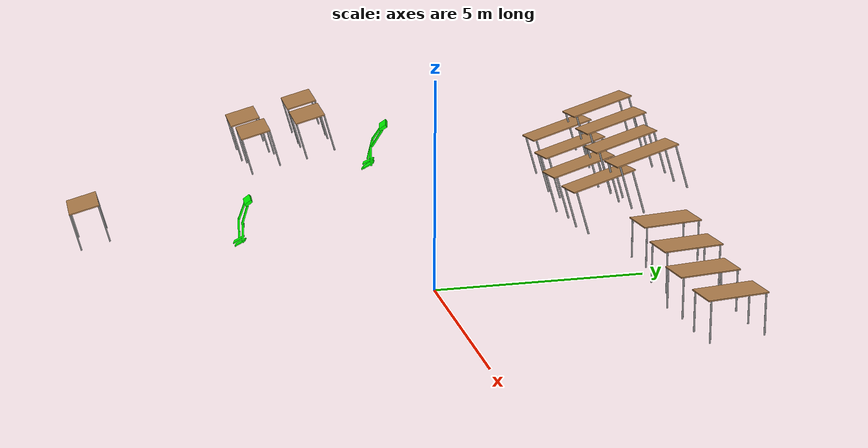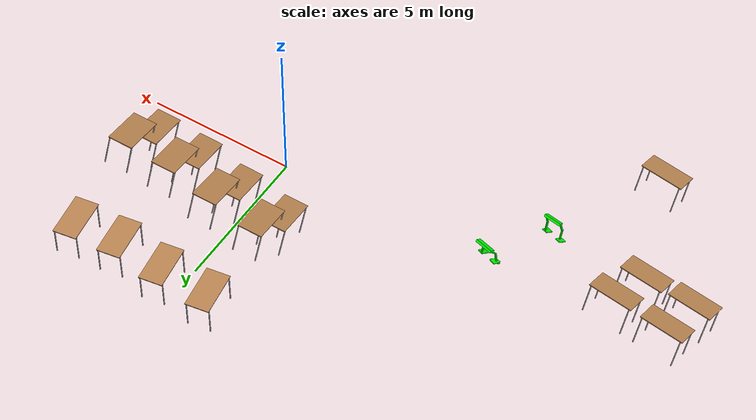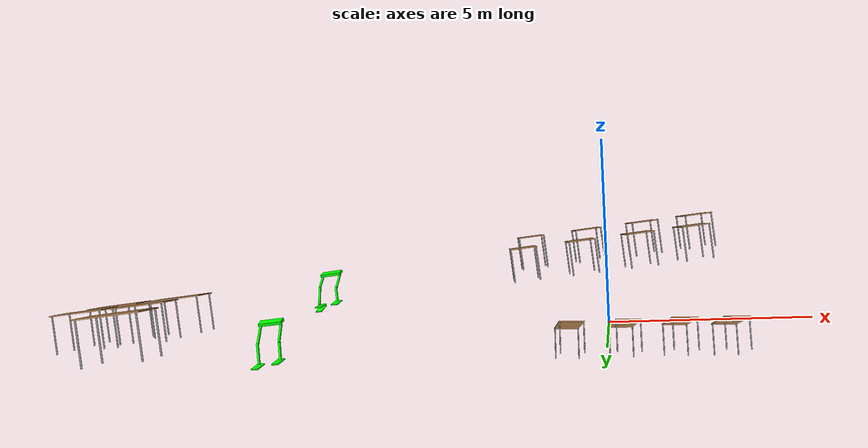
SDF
<?xml version='1.0'?>
<sdf version='1.6'>
  <model name='model'>
    <model name='model'>
      <model name='model'>
        <link name='link_0'>
          <pose frame=''>-6.17867 2.41501 0.938772 -0.011582 -0.334231 1.40503</pose>
          <inertial>
            <mass>1</mass>
            <inertia>
              <ixx>0.166667</ixx>
              <ixy>0</ixy>
              <ixz>0</ixz>
              <iyy>0.166667</iyy>
              <iyz>0</iyz>
              <izz>0.166667</izz>
            </inertia>
            <pose frame=''>0 0 0 0 -0 0</pose>
          </inertial>
          <self_collide>0</self_collide>
          <kinematic>0</kinematic>
          <visual name='visual'>
            <pose frame=''>0 0 0 0 -0 0</pose>
            <geometry>
              <box>
                <size>0.2 0.6 0.08</size>
              </box>
            </geometry>
            <material>
              <lighting>1</lighting>
              <script>
                <uri>file://media/materials/scripts/gazebo.material</uri>
                <name>Gazebo/Grey</name>
              </script>
              <shader type='pixel'>
                <normal_map>__default__</normal_map>
              </shader>
              <ambient>0 1 0 0</ambient>
              <diffuse>0 1 0 0</diffuse>
              <specular>0 1 0.01 0</specular>
              <emissive>0 0 0 1</emissive>
            </material>
            <transparency>0</transparency>
            <cast_shadows>1</cast_shadows>
          </visual>
          <collision name='collision'>
            <laser_retro>0</laser_retro>
            <max_contacts>10</max_contacts>
            <pose frame=''>0 0 0 0 -0 0</pose>
            <geometry>
              <box>
                <size>0.2 0.6 0.08</size>
              </box>
            </geometry>
            <surface>
              <friction>
                <ode>
                  <mu>1</mu>
                  <mu2>1</mu2>
                  <fdir1>0 0 0</fdir1>
                  <slip1>0</slip1>
                  <slip2>0</slip2>
                </ode>
                <torsional>
                  <coefficient>1</coefficient>
                  <patch_radius>0</patch_radius>
                  <surface_radius>0</surface_radius>
                  <use_patch_radius>1</use_patch_radius>
                  <ode>
                    <slip>0</slip>
                  </ode>
                </torsional>
              </friction>
              <bounce>
                <restitution_coefficient>0</restitution_coefficient>
                <threshold>1e+06</threshold>
              </bounce>
              <contact>
                <collide_without_contact>0</collide_without_contact>
                <collide_without_contact_bitmask>1</collide_without_contact_bitmask>
                <collide_bitmask>1</collide_bitmask>
                <ode>
                  <soft_cfm>0</soft_cfm>
                  <soft_erp>0.2</soft_erp>
                  <kp>1e+13</kp>
                  <kd>1</kd>
                  <max_vel>0.01</max_vel>
                  <min_depth>0</min_depth>
                </ode>
                <bullet>
                  <split_impulse>1</split_impulse>
                  <split_impulse_penetration_threshold>-0.01</split_impulse_penetration_threshold>
                  <soft_cfm>0</soft_cfm>
                  <soft_erp>0.2</soft_erp>
                  <kp>1e+13</kp>
                  <kd>1</kd>
                </bullet>
              </contact>
            </surface>
          </collision>
        </link>
        <link name='link_0_clone'>
          <pose frame=''>-6.58153 -1.3868 0.046294 -0.00055 -0.365456 1.52859</pose>
          <inertial>
            <mass>1</mass>
            <inertia>
              <ixx>0.166667</ixx>
              <ixy>0</ixy>
              <ixz>0</ixz>
              <iyy>0.166667</iyy>
              <iyz>0</iyz>
              <izz>0.166667</izz>
            </inertia>
            <pose frame=''>0 0 0 0 -0 0</pose>
          </inertial>
          <self_collide>0</self_collide>
          <kinematic>0</kinematic>
          <visual name='visual'>
            <pose frame=''>0 0 0 0 -0 0</pose>
            <geometry>
              <box>
                <size>0.2 0.6 0.08</size>
              </box>
            </geometry>
            <material>
              <lighting>1</lighting>
              <script>
                <uri>file://media/materials/scripts/gazebo.material</uri>
                <name>Gazebo/Grey</name>
              </script>
              <shader type='pixel'>
                <normal_map>__default__</normal_map>
              </shader>
              <ambient>0 1 0 0</ambient>
              <diffuse>0 1 0 0</diffuse>
              <specular>0 1 0.01 0</specular>
              <emissive>0 0 0 1</emissive>
            </material>
            <transparency>0</transparency>
            <cast_shadows>1</cast_shadows>
          </visual>
          <collision name='collision'>
            <laser_retro>0</laser_retro>
            <max_contacts>10</max_contacts>
            <pose frame=''>0 0 0 0 -0 0</pose>
            <geometry>
              <box>
                <size>0.2 0.6 0.08</size>
              </box>
            </geometry>
            <surface>
              <friction>
                <ode>
                  <mu>1</mu>
                  <mu2>1</mu2>
                  <fdir1>0 0 0</fdir1>
                  <slip1>0</slip1>
                  <slip2>0</slip2>
                </ode>
                <torsional>
                  <coefficient>1</coefficient>
                  <patch_radius>0</patch_radius>
                  <surface_radius>0</surface_radius>
                  <use_patch_radius>1</use_patch_radius>
                  <ode>
                    <slip>0</slip>
                  </ode>
                </torsional>
              </friction>
              <bounce>
                <restitution_coefficient>0</restitution_coefficient>
                <threshold>1e+06</threshold>
              </bounce>
              <contact>
                <collide_without_contact>0</collide_without_contact>
                <collide_without_contact_bitmask>1</collide_without_contact_bitmask>
                <collide_bitmask>1</collide_bitmask>
                <ode>
                  <soft_cfm>0</soft_cfm>
                  <soft_erp>0.2</soft_erp>
                  <kp>1e+13</kp>
                  <kd>1</kd>
                  <max_vel>0.01</max_vel>
                  <min_depth>0</min_depth>
                </ode>
                <bullet>
                  <split_impulse>1</split_impulse>
                  <split_impulse_penetration_threshold>-0.01</split_impulse_penetration_threshold>
                  <soft_cfm>0</soft_cfm>
                  <soft_erp>0.2</soft_erp>
                  <kp>1e+13</kp>
                  <kd>1</kd>
                </bullet>
              </contact>
            </surface>
          </collision>
        </link>
        <link name='link_1'>
          <pose frame=''>-6.41046 1.8165 0.1133 0.183046 -0 -0.235467</pose>
          <inertial>
            <mass>1</mass>
            <inertia>
              <ixx>0.166667</ixx>
              <ixy>0</ixy>
              <ixz>0</ixz>
              <iyy>0.166667</iyy>
              <iyz>0</iyz>
              <izz>0.166667</izz>
            </inertia>
            <pose frame=''>0 0 0 0 -0 0</pose>
          </inertial>
          <self_collide>0</self_collide>
          <kinematic>0</kinematic>
          <visual name='visual'>
            <pose frame=''>0 0 0 0 -0 0</pose>
            <geometry>
              <box>
                <size>0.2 0.3 0.03</size>
              </box>
            </geometry>
            <material>
              <lighting>1</lighting>
              <script>
                <uri>file://media/materials/scripts/gazebo.material</uri>
                <name>Gazebo/Grey</name>
              </script>
              <shader type='pixel'>
                <normal_map>__default__</normal_map>
              </shader>
              <ambient>0 1 0 0</ambient>
              <diffuse>0 1 0 0</diffuse>
              <specular>0.01 0.01 0.01 1</specular>
              <emissive>0 0 0 1</emissive>
            </material>
            <transparency>0</transparency>
            <cast_shadows>1</cast_shadows>
          </visual>
          <collision name='collision'>
            <laser_retro>0</laser_retro>
            <max_contacts>10</max_contacts>
            <pose frame=''>0 0 0 0 -0 0</pose>
            <geometry>
              <box>
                <size>0.2 0.3 0.03</size>
              </box>
            </geometry>
            <surface>
              <friction>
                <ode>
                  <mu>1</mu>
                  <mu2>1</mu2>
                  <fdir1>0 0 0</fdir1>
                  <slip1>0</slip1>
                  <slip2>0</slip2>
                </ode>
                <torsional>
                  <coefficient>1</coefficient>
                  <patch_radius>0</patch_radius>
                  <surface_radius>0</surface_radius>
                  <use_patch_radius>1</use_patch_radius>
                  <ode>
                    <slip>0</slip>
                  </ode>
                </torsional>
              </friction>
              <bounce>
                <restitution_coefficient>0</restitution_coefficient>
                <threshold>1e+06</threshold>
              </bounce>
              <contact>
                <collide_without_contact>0</collide_without_contact>
                <collide_without_contact_bitmask>1</collide_without_contact_bitmask>
                <collide_bitmask>1</collide_bitmask>
                <ode>
                  <soft_cfm>0</soft_cfm>
                  <soft_erp>0.2</soft_erp>
                  <kp>1e+13</kp>
                  <kd>1</kd>
                  <max_vel>0.01</max_vel>
                  <min_depth>0</min_depth>
                </ode>
                <bullet>
                  <split_impulse>1</split_impulse>
                  <split_impulse_penetration_threshold>-0.01</split_impulse_penetration_threshold>
                  <soft_cfm>0</soft_cfm>
                  <soft_erp>0.2</soft_erp>
                  <kp>1e+13</kp>
                  <kd>1</kd>
                </bullet>
              </contact>
            </surface>
          </collision>
        </link>
        <link name='link_1_clone'>
          <pose frame=''>-5.92798 1.76459 0.152262 0.281576 0.047119 -0.221842</pose>
          <inertial>
            <mass>1</mass>
            <inertia>
              <ixx>0.166667</ixx>
              <ixy>0</ixy>
              <ixz>0</ixz>
              <iyy>0.166667</iyy>
              <iyz>0</iyz>
              <izz>0.166667</izz>
            </inertia>
            <pose frame=''>0 0 0 0 -0 0</pose>
          </inertial>
          <self_collide>0</self_collide>
          <kinematic>0</kinematic>
          <visual name='visual'>
            <pose frame=''>0 0 0 0 -0 0</pose>
            <geometry>
              <box>
                <size>0.2 0.3 0.03</size>
              </box>
            </geometry>
            <material>
              <lighting>1</lighting>
              <script>
                <uri>file://media/materials/scripts/gazebo.material</uri>
                <name>Gazebo/Grey</name>
              </script>
              <shader type='pixel'>
                <normal_map>__default__</normal_map>
              </shader>
              <ambient>0 1 0 0</ambient>
              <diffuse>0 1 0 0</diffuse>
              <specular>0 1 0 0</specular>
              <emissive>0 0 0 1</emissive>
            </material>
            <transparency>0</transparency>
            <cast_shadows>1</cast_shadows>
          </visual>
          <collision name='collision'>
            <laser_retro>0</laser_retro>
            <max_contacts>10</max_contacts>
            <pose frame=''>0 0 0 0 -0 0</pose>
            <geometry>
              <box>
                <size>0.2 0.3 0.03</size>
              </box>
            </geometry>
            <surface>
              <friction>
                <ode>
                  <mu>1</mu>
                  <mu2>1</mu2>
                  <fdir1>0 0 0</fdir1>
                  <slip1>0</slip1>
                  <slip2>0</slip2>
                </ode>
                <torsional>
                  <coefficient>1</coefficient>
                  <patch_radius>0</patch_radius>
                  <surface_radius>0</surface_radius>
                  <use_patch_radius>1</use_patch_radius>
                  <ode>
                    <slip>0</slip>
                  </ode>
                </torsional>
              </friction>
              <bounce>
                <restitution_coefficient>0</restitution_coefficient>
                <threshold>1e+06</threshold>
              </bounce>
              <contact>
                <collide_without_contact>0</collide_without_contact>
                <collide_without_contact_bitmask>1</collide_without_contact_bitmask>
                <collide_bitmask>1</collide_bitmask>
                <ode>
                  <soft_cfm>0</soft_cfm>
                  <soft_erp>0.2</soft_erp>
                  <kp>1e+13</kp>
                  <kd>1</kd>
                  <max_vel>0.01</max_vel>
                  <min_depth>0</min_depth>
                </ode>
                <bullet>
                  <split_impulse>1</split_impulse>
                  <split_impulse_penetration_threshold>-0.01</split_impulse_penetration_threshold>
                  <soft_cfm>0</soft_cfm>
                  <soft_erp>0.2</soft_erp>
                  <kp>1e+13</kp>
                  <kd>1</kd>
                </bullet>
              </contact>
            </surface>
          </collision>
        </link>
        <link name='link_1_clone_0'>
          <pose frame=''>-6.38012 1.74212 0.040313 0.455747 -0.004913 -0.290917</pose>
          <inertial>
            <mass>1</mass>
            <inertia>
              <ixx>0.166667</ixx>
              <ixy>0</ixy>
              <ixz>0</ixz>
              <iyy>0.166667</iyy>
              <iyz>0</iyz>
              <izz>0.166667</izz>
            </inertia>
            <pose frame=''>0 0 0 0 -0 0</pose>
          </inertial>
          <self_collide>0</self_collide>
          <kinematic>0</kinematic>
          <visual name='visual'>
            <pose frame=''>0 0 0 0 -0 0</pose>
            <geometry>
              <box>
                <size>0.2 0.3 0.03</size>
              </box>
            </geometry>
            <material>
              <lighting>1</lighting>
              <script>
                <uri>file://media/materials/scripts/gazebo.material</uri>
                <name>Gazebo/Grey</name>
              </script>
              <shader type='pixel'>
                <normal_map>__default__</normal_map>
              </shader>
              <ambient>0 1 0 0</ambient>
              <diffuse>0 1 0 0</diffuse>
              <specular>0.01 0.01 0.01 1</specular>
              <emissive>0 0 0 1</emissive>
            </material>
            <transparency>0</transparency>
            <cast_shadows>1</cast_shadows>
          </visual>
          <collision name='collision'>
            <laser_retro>0</laser_retro>
            <max_contacts>10</max_contacts>
            <pose frame=''>0 0 0 0 -0 0</pose>
            <geometry>
              <box>
                <size>0.2 0.3 0.03</size>
              </box>
            </geometry>
            <surface>
              <friction>
                <ode>
                  <mu>1</mu>
                  <mu2>1</mu2>
                  <fdir1>0 0 0</fdir1>
                  <slip1>0</slip1>
                  <slip2>0</slip2>
                </ode>
                <torsional>
                  <coefficient>1</coefficient>
                  <patch_radius>0</patch_radius>
                  <surface_radius>0</surface_radius>
                  <use_patch_radius>1</use_patch_radius>
                  <ode>
                    <slip>0</slip>
                  </ode>
                </torsional>
              </friction>
              <bounce>
                <restitution_coefficient>0</restitution_coefficient>
                <threshold>1e+06</threshold>
              </bounce>
              <contact>
                <collide_without_contact>0</collide_without_contact>
                <collide_without_contact_bitmask>1</collide_without_contact_bitmask>
                <collide_bitmask>1</collide_bitmask>
                <ode>
                  <soft_cfm>0</soft_cfm>
                  <soft_erp>0.2</soft_erp>
                  <kp>1e+13</kp>
                  <kd>1</kd>
                  <max_vel>0.01</max_vel>
                  <min_depth>0</min_depth>
                </ode>
                <bullet>
                  <split_impulse>1</split_impulse>
                  <split_impulse_penetration_threshold>-0.01</split_impulse_penetration_threshold>
                  <soft_cfm>0</soft_cfm>
                  <soft_erp>0.2</soft_erp>
                  <kp>1e+13</kp>
                  <kd>1</kd>
                </bullet>
              </contact>
            </surface>
          </collision>
        </link>
        <link name='link_1_clone_clone'>
          <pose frame=''>-6.33133 -1.88437 -0.865745 0.271134 0.012393 -0.271892</pose>
          <inertial>
            <mass>1</mass>
            <inertia>
              <ixx>0.166667</ixx>
              <ixy>0</ixy>
              <ixz>0</ixz>
              <iyy>0.166667</iyy>
              <iyz>0</iyz>
              <izz>0.166667</izz>
            </inertia>
            <pose frame=''>0 0 0 0 -0 0</pose>
          </inertial>
          <self_collide>0</self_collide>
          <kinematic>0</kinematic>
          <visual name='visual'>
            <pose frame=''>0 0 0 0 -0 0</pose>
            <geometry>
              <box>
                <size>0.2 0.3 0.03</size>
              </box>
            </geometry>
            <material>
              <lighting>1</lighting>
              <script>
                <uri>file://media/materials/scripts/gazebo.material</uri>
                <name>Gazebo/Grey</name>
              </script>
              <shader type='pixel'>
                <normal_map>__default__</normal_map>
              </shader>
              <ambient>0 1 0 0</ambient>
              <diffuse>0 1 0 0</diffuse>
              <specular>0 1 0 0</specular>
              <emissive>0 0 0 1</emissive>
            </material>
            <transparency>0</transparency>
            <cast_shadows>1</cast_shadows>
          </visual>
          <collision name='collision'>
            <laser_retro>0</laser_retro>
            <max_contacts>10</max_contacts>
            <pose frame=''>0 0 0 0 -0 0</pose>
            <geometry>
              <box>
                <size>0.2 0.3 0.03</size>
              </box>
            </geometry>
            <surface>
              <friction>
                <ode>
                  <mu>1</mu>
                  <mu2>1</mu2>
                  <fdir1>0 0 0</fdir1>
                  <slip1>0</slip1>
                  <slip2>0</slip2>
                </ode>
                <torsional>
                  <coefficient>1</coefficient>
                  <patch_radius>0</patch_radius>
                  <surface_radius>0</surface_radius>
                  <use_patch_radius>1</use_patch_radius>
                  <ode>
                    <slip>0</slip>
                  </ode>
                </torsional>
              </friction>
              <bounce>
                <restitution_coefficient>0</restitution_coefficient>
                <threshold>1e+06</threshold>
              </bounce>
              <contact>
                <collide_without_contact>0</collide_without_contact>
                <collide_without_contact_bitmask>1</collide_without_contact_bitmask>
                <collide_bitmask>1</collide_bitmask>
                <ode>
                  <soft_cfm>0</soft_cfm>
                  <soft_erp>0.2</soft_erp>
                  <kp>1e+13</kp>
                  <kd>1</kd>
                  <max_vel>0.01</max_vel>
                  <min_depth>0</min_depth>
                </ode>
                <bullet>
                  <split_impulse>1</split_impulse>
                  <split_impulse_penetration_threshold>-0.01</split_impulse_penetration_threshold>
                  <soft_cfm>0</soft_cfm>
                  <soft_erp>0.2</soft_erp>
                  <kp>1e+13</kp>
                  <kd>1</kd>
                </bullet>
              </contact>
            </surface>
          </collision>
        </link>
        <link name='link_1_clone_clone_0'>
          <pose frame=''>-6.85274 -1.88855 -0.927168 0.267157 0.036796 -0.265104</pose>
          <inertial>
            <mass>1</mass>
            <inertia>
              <ixx>0.166667</ixx>
              <ixy>0</ixy>
              <ixz>0</ixz>
              <iyy>0.166667</iyy>
              <iyz>0</iyz>
              <izz>0.166667</izz>
            </inertia>
            <pose frame=''>0 0 0 0 -0 0</pose>
          </inertial>
          <self_collide>0</self_collide>
          <kinematic>0</kinematic>
          <visual name='visual'>
            <pose frame=''>0 0 0 0 -0 0</pose>
            <geometry>
              <box>
                <size>0.2 0.3 0.03</size>
              </box>
            </geometry>
            <material>
              <lighting>1</lighting>
              <script>
                <uri>file://media/materials/scripts/gazebo.material</uri>
                <name>Gazebo/Grey</name>
              </script>
              <shader type='pixel'>
                <normal_map>__default__</normal_map>
              </shader>
              <ambient>0 1 0 0</ambient>
              <diffuse>0 1 0 0</diffuse>
              <specular>0 1 0 0</specular>
              <emissive>0 0 0 1</emissive>
            </material>
            <transparency>0</transparency>
            <cast_shadows>1</cast_shadows>
          </visual>
          <collision name='collision'>
            <laser_retro>0</laser_retro>
            <max_contacts>10</max_contacts>
            <pose frame=''>0 0 0 0 -0 0</pose>
            <geometry>
              <box>
                <size>0.2 0.3 0.03</size>
              </box>
            </geometry>
            <surface>
              <friction>
                <ode>
                  <mu>1</mu>
                  <mu2>1</mu2>
                  <fdir1>0 0 0</fdir1>
                  <slip1>0</slip1>
                  <slip2>0</slip2>
                </ode>
                <torsional>
                  <coefficient>1</coefficient>
                  <patch_radius>0</patch_radius>
                  <surface_radius>0</surface_radius>
                  <use_patch_radius>1</use_patch_radius>
                  <ode>
                    <slip>0</slip>
                  </ode>
                </torsional>
              </friction>
              <bounce>
                <restitution_coefficient>0</restitution_coefficient>
                <threshold>1e+06</threshold>
              </bounce>
              <contact>
                <collide_without_contact>0</collide_without_contact>
                <collide_without_contact_bitmask>1</collide_without_contact_bitmask>
                <collide_bitmask>1</collide_bitmask>
                <ode>
                  <soft_cfm>0</soft_cfm>
                  <soft_erp>0.2</soft_erp>
                  <kp>1e+13</kp>
                  <kd>1</kd>
                  <max_vel>0.01</max_vel>
                  <min_depth>0</min_depth>
                </ode>
                <bullet>
                  <split_impulse>1</split_impulse>
                  <split_impulse_penetration_threshold>-0.01</split_impulse_penetration_threshold>
                  <soft_cfm>0</soft_cfm>
                  <soft_erp>0.2</soft_erp>
                  <kp>1e+13</kp>
                  <kd>1</kd>
                </bullet>
              </contact>
            </surface>
          </collision>
        </link>
        <link name='link_2'>
          <pose frame=''>-6.44305 2.26627 0.760746 -0.891241 0.080792 0.00706</pose>
          <inertial>
            <mass>1</mass>
            <inertia>
              <ixx>0.166667</ixx>
              <ixy>0</ixy>
              <ixz>0</ixz>
              <iyy>0.166667</iyy>
              <iyz>0</iyz>
              <izz>0.166667</izz>
            </inertia>
            <pose frame=''>0 0 0 0 -0 0</pose>
          </inertial>
          <self_collide>0</self_collide>
          <kinematic>0</kinematic>
          <visual name='visual'>
            <pose frame=''>0 0 0 0 -0 0</pose>
            <geometry>
              <box>
                <size>0.05 0.05 0.5</size>
              </box>
            </geometry>
            <material>
              <lighting>1</lighting>
              <script>
                <uri>file://media/materials/scripts/gazebo.material</uri>
                <name>Gazebo/Grey</name>
              </script>
              <shader type='pixel'>
                <normal_map>__default__</normal_map>
              </shader>
              <ambient>0 1 0 0</ambient>
              <diffuse>0 1 0 0</diffuse>
              <specular>0.01 0.01 0.01 1</specular>
              <emissive>0 0 0 1</emissive>
            </material>
            <transparency>0</transparency>
            <cast_shadows>1</cast_shadows>
          </visual>
          <collision name='collision'>
            <laser_retro>0</laser_retro>
            <max_contacts>10</max_contacts>
            <pose frame=''>0 0 0 0 -0 0</pose>
            <geometry>
              <box>
                <size>0.05 0.05 0.5</size>
              </box>
            </geometry>
            <surface>
              <friction>
                <ode>
                  <mu>1</mu>
                  <mu2>1</mu2>
                  <fdir1>0 0 0</fdir1>
                  <slip1>0</slip1>
                  <slip2>0</slip2>
                </ode>
                <torsional>
                  <coefficient>1</coefficient>
                  <patch_radius>0</patch_radius>
                  <surface_radius>0</surface_radius>
                  <use_patch_radius>1</use_patch_radius>
                  <ode>
                    <slip>0</slip>
                  </ode>
                </torsional>
              </friction>
              <bounce>
                <restitution_coefficient>0</restitution_coefficient>
                <threshold>1e+06</threshold>
              </bounce>
              <contact>
                <collide_without_contact>0</collide_without_contact>
                <collide_without_contact_bitmask>1</collide_without_contact_bitmask>
                <collide_bitmask>1</collide_bitmask>
                <ode>
                  <soft_cfm>0</soft_cfm>
                  <soft_erp>0.2</soft_erp>
                  <kp>1e+13</kp>
                  <kd>1</kd>
                  <max_vel>0.01</max_vel>
                  <min_depth>0</min_depth>
                </ode>
                <bullet>
                  <split_impulse>1</split_impulse>
                  <split_impulse_penetration_threshold>-0.01</split_impulse_penetration_threshold>
                  <soft_cfm>0</soft_cfm>
                  <soft_erp>0.2</soft_erp>
                  <kp>1e+13</kp>
                  <kd>1</kd>
                </bullet>
              </contact>
            </surface>
          </collision>
        </link>
        <link name='link_2_clone'>
          <pose frame=''>-6.44658 1.94399 0.378339 -0.522527 -0.030013 -0.031139</pose>
          <inertial>
            <mass>1</mass>
            <inertia>
              <ixx>0.166667</ixx>
              <ixy>0</ixy>
              <ixz>0</ixz>
              <iyy>0.166667</iyy>
              <iyz>0</iyz>
              <izz>0.166667</izz>
            </inertia>
            <pose frame=''>0 0 0 0 -0 0</pose>
          </inertial>
          <self_collide>0</self_collide>
          <kinematic>0</kinematic>
          <visual name='visual'>
            <pose frame=''>0 0 0 0 -0 0</pose>
            <geometry>
              <box>
                <size>0.05 0.05 0.5</size>
              </box>
            </geometry>
            <material>
              <lighting>1</lighting>
              <script>
                <uri>file://media/materials/scripts/gazebo.material</uri>
                <name>Gazebo/Grey</name>
              </script>
              <shader type='pixel'>
                <normal_map>__default__</normal_map>
              </shader>
              <ambient>0.3 0.3 0.3 1</ambient>
              <diffuse>0 1 0 1</diffuse>
              <specular>0 1 0 1</specular>
              <emissive>0 0 0 1</emissive>
            </material>
            <transparency>0</transparency>
            <cast_shadows>1</cast_shadows>
          </visual>
          <collision name='collision'>
            <laser_retro>0</laser_retro>
            <max_contacts>10</max_contacts>
            <pose frame=''>0 0 0 0 -0 0</pose>
            <geometry>
              <box>
                <size>0.05 0.05 0.5</size>
              </box>
            </geometry>
            <surface>
              <friction>
                <ode>
                  <mu>1</mu>
                  <mu2>1</mu2>
                  <fdir1>0 0 0</fdir1>
                  <slip1>0</slip1>
                  <slip2>0</slip2>
                </ode>
                <torsional>
                  <coefficient>1</coefficient>
                  <patch_radius>0</patch_radius>
                  <surface_radius>0</surface_radius>
                  <use_patch_radius>1</use_patch_radius>
                  <ode>
                    <slip>0</slip>
                  </ode>
                </torsional>
              </friction>
              <bounce>
                <restitution_coefficient>0</restitution_coefficient>
                <threshold>1e+06</threshold>
              </bounce>
              <contact>
                <collide_without_contact>0</collide_without_contact>
                <collide_without_contact_bitmask>1</collide_without_contact_bitmask>
                <collide_bitmask>1</collide_bitmask>
                <ode>
                  <soft_cfm>0</soft_cfm>
                  <soft_erp>0.2</soft_erp>
                  <kp>1e+13</kp>
                  <kd>1</kd>
                  <max_vel>0.01</max_vel>
                  <min_depth>0</min_depth>
                </ode>
                <bullet>
                  <split_impulse>1</split_impulse>
                  <split_impulse_penetration_threshold>-0.01</split_impulse_penetration_threshold>
                  <soft_cfm>0</soft_cfm>
                  <soft_erp>0.2</soft_erp>
                  <kp>1e+13</kp>
                  <kd>1</kd>
                </bullet>
              </contact>
            </surface>
          </collision>
        </link>
        <link name='link_2_clone_0'>
          <pose frame=''>-5.92263 2.15206 0.732218 -0.837517 0.080791 0.00706</pose>
          <inertial>
            <mass>1</mass>
            <inertia>
              <ixx>0.166667</ixx>
              <ixy>0</ixy>
              <ixz>0</ixz>
              <iyy>0.166667</iyy>
              <iyz>0</iyz>
              <izz>0.166667</izz>
            </inertia>
            <pose frame=''>0 0 0 0 -0 0</pose>
          </inertial>
          <self_collide>0</self_collide>
          <kinematic>0</kinematic>
          <visual name='visual'>
            <pose frame=''>0 0 0 0 -0 0</pose>
            <geometry>
              <box>
                <size>0.05 0.05 0.5</size>
              </box>
            </geometry>
            <material>
              <lighting>1</lighting>
              <script>
                <uri>file://media/materials/scripts/gazebo.material</uri>
                <name>Gazebo/Grey</name>
              </script>
              <shader type='pixel'>
                <normal_map>__default__</normal_map>
              </shader>
              <ambient>0 1 0 0</ambient>
              <diffuse>0 1 0 0</diffuse>
              <specular>0 1 0 0</specular>
              <emissive>0 0 0 1</emissive>
            </material>
            <transparency>0</transparency>
            <cast_shadows>1</cast_shadows>
          </visual>
          <collision name='collision'>
            <laser_retro>0</laser_retro>
            <max_contacts>10</max_contacts>
            <pose frame=''>0 0 0 0 -0 0</pose>
            <geometry>
              <box>
                <size>0.05 0.05 0.5</size>
              </box>
            </geometry>
            <surface>
              <friction>
                <ode>
                  <mu>1</mu>
                  <mu2>1</mu2>
                  <fdir1>0 0 0</fdir1>
                  <slip1>0</slip1>
                  <slip2>0</slip2>
                </ode>
                <torsional>
                  <coefficient>1</coefficient>
                  <patch_radius>0</patch_radius>
                  <surface_radius>0</surface_radius>
                  <use_patch_radius>1</use_patch_radius>
                  <ode>
                    <slip>0</slip>
                  </ode>
                </torsional>
              </friction>
              <bounce>
                <restitution_coefficient>0</restitution_coefficient>
                <threshold>1e+06</threshold>
              </bounce>
              <contact>
                <collide_without_contact>0</collide_without_contact>
                <collide_without_contact_bitmask>1</collide_without_contact_bitmask>
                <collide_bitmask>1</collide_bitmask>
                <ode>
                  <soft_cfm>0</soft_cfm>
                  <soft_erp>0.2</soft_erp>
                  <kp>1e+13</kp>
                  <kd>1</kd>
                  <max_vel>0.01</max_vel>
                  <min_depth>0</min_depth>
                </ode>
                <bullet>
                  <split_impulse>1</split_impulse>
                  <split_impulse_penetration_threshold>-0.01</split_impulse_penetration_threshold>
                  <soft_cfm>0</soft_cfm>
                  <soft_erp>0.2</soft_erp>
                  <kp>1e+13</kp>
                  <kd>1</kd>
                </bullet>
              </contact>
            </surface>
          </collision>
        </link>
        <link name='link_2_clone_0_clone'>
          <pose frame=''>-6.31307 -1.5775 -0.220206 -0.574205 0.008496 -0.035888</pose>
          <inertial>
            <mass>1</mass>
            <inertia>
              <ixx>0.166667</ixx>
              <ixy>0</ixy>
              <ixz>0</ixz>
              <iyy>0.166667</iyy>
              <iyz>0</iyz>
              <izz>0.166667</izz>
            </inertia>
            <pose frame=''>0 0 0 0 -0 0</pose>
          </inertial>
          <self_collide>0</self_collide>
          <kinematic>0</kinematic>
          <visual name='visual'>
            <pose frame=''>0 0 0 0 -0 0</pose>
            <geometry>
              <box>
                <size>0.05 0.05 0.5</size>
              </box>
            </geometry>
            <material>
              <lighting>1</lighting>
              <script>
                <uri>file://media/materials/scripts/gazebo.material</uri>
                <name>Gazebo/Grey</name>
              </script>
              <shader type='pixel'>
                <normal_map>__default__</normal_map>
              </shader>
              <ambient>0 1 0 0</ambient>
              <diffuse>0 1 0 0</diffuse>
              <specular>0 1 0 0</specular>
              <emissive>0 0 0 1</emissive>
            </material>
            <transparency>0</transparency>
            <cast_shadows>1</cast_shadows>
          </visual>
          <collision name='collision'>
            <laser_retro>0</laser_retro>
            <max_contacts>10</max_contacts>
            <pose frame=''>0 0 0 0 -0 0</pose>
            <geometry>
              <box>
                <size>0.05 0.05 0.5</size>
              </box>
            </geometry>
            <surface>
              <friction>
                <ode>
                  <mu>1</mu>
                  <mu2>1</mu2>
                  <fdir1>0 0 0</fdir1>
                  <slip1>0</slip1>
                  <slip2>0</slip2>
                </ode>
                <torsional>
                  <coefficient>1</coefficient>
                  <patch_radius>0</patch_radius>
                  <surface_radius>0</surface_radius>
                  <use_patch_radius>1</use_patch_radius>
                  <ode>
                    <slip>0</slip>
                  </ode>
                </torsional>
              </friction>
              <bounce>
                <restitution_coefficient>0</restitution_coefficient>
                <threshold>1e+06</threshold>
              </bounce>
              <contact>
                <collide_without_contact>0</collide_without_contact>
                <collide_without_contact_bitmask>1</collide_without_contact_bitmask>
                <collide_bitmask>1</collide_bitmask>
                <ode>
                  <soft_cfm>0</soft_cfm>
                  <soft_erp>0.2</soft_erp>
                  <kp>1e+13</kp>
                  <kd>1</kd>
                  <max_vel>0.01</max_vel>
                  <min_depth>0</min_depth>
                </ode>
                <bullet>
                  <split_impulse>1</split_impulse>
                  <split_impulse_penetration_threshold>-0.01</split_impulse_penetration_threshold>
                  <soft_cfm>0</soft_cfm>
                  <soft_erp>0.2</soft_erp>
                  <kp>1e+13</kp>
                  <kd>1</kd>
                </bullet>
              </contact>
            </surface>
          </collision>
        </link>
        <link name='link_2_clone_1'>
          <pose frame=''>-6.84229 -1.5856 -0.213701 -0.627932 0.008497 -0.035888</pose>
          <inertial>
            <mass>1</mass>
            <inertia>
              <ixx>0.166667</ixx>
              <ixy>0</ixy>
              <ixz>0</ixz>
              <iyy>0.166667</iyy>
              <iyz>0</iyz>
              <izz>0.166667</izz>
            </inertia>
            <pose frame=''>0 0 0 0 -0 0</pose>
          </inertial>
          <self_collide>0</self_collide>
          <kinematic>0</kinematic>
          <visual name='visual'>
            <pose frame=''>0 0 0 0 -0 0</pose>
            <geometry>
              <box>
                <size>0.05 0.05 0.5</size>
              </box>
            </geometry>
            <material>
              <lighting>1</lighting>
              <script>
                <uri>file://media/materials/scripts/gazebo.material</uri>
                <name>Gazebo/Grey</name>
              </script>
              <shader type='pixel'>
                <normal_map>__default__</normal_map>
              </shader>
              <ambient>0 1 0 0</ambient>
              <diffuse>0 1 0 0</diffuse>
              <specular>0.01 0.01 0.01 1</specular>
              <emissive>0 0 0 1</emissive>
            </material>
            <transparency>0</transparency>
            <cast_shadows>1</cast_shadows>
          </visual>
          <collision name='collision'>
            <laser_retro>0</laser_retro>
            <max_contacts>10</max_contacts>
            <pose frame=''>0 0 0 0 -0 0</pose>
            <geometry>
              <box>
                <size>0.05 0.05 0.5</size>
              </box>
            </geometry>
            <surface>
              <friction>
                <ode>
                  <mu>1</mu>
                  <mu2>1</mu2>
                  <fdir1>0 0 0</fdir1>
                  <slip1>0</slip1>
                  <slip2>0</slip2>
                </ode>
                <torsional>
                  <coefficient>1</coefficient>
                  <patch_radius>0</patch_radius>
                  <surface_radius>0</surface_radius>
                  <use_patch_radius>1</use_patch_radius>
                  <ode>
                    <slip>0</slip>
                  </ode>
                </torsional>
              </friction>
              <bounce>
                <restitution_coefficient>0</restitution_coefficient>
                <threshold>1e+06</threshold>
              </bounce>
              <contact>
                <collide_without_contact>0</collide_without_contact>
                <collide_without_contact_bitmask>1</collide_without_contact_bitmask>
                <collide_bitmask>1</collide_bitmask>
                <ode>
                  <soft_cfm>0</soft_cfm>
                  <soft_erp>0.2</soft_erp>
                  <kp>1e+13</kp>
                  <kd>1</kd>
                  <max_vel>0.01</max_vel>
                  <min_depth>0</min_depth>
                </ode>
                <bullet>
                  <split_impulse>1</split_impulse>
                  <split_impulse_penetration_threshold>-0.01</split_impulse_penetration_threshold>
                  <soft_cfm>0</soft_cfm>
                  <soft_erp>0.2</soft_erp>
                  <kp>1e+13</kp>
                  <kd>1</kd>
                </bullet>
              </contact>
            </surface>
          </collision>
        </link>
        <link name='link_2_clone_clone'>
          <pose frame=''>-5.93174 1.87683 0.341136 -0.255605 -0.088448 -0.101816</pose>
          <inertial>
            <mass>1</mass>
            <inertia>
              <ixx>0.166667</ixx>
              <ixy>0</ixy>
              <ixz>0</ixz>
              <iyy>0.166667</iyy>
              <iyz>0</iyz>
              <izz>0.166667</izz>
            </inertia>
            <pose frame=''>0 0 0 0 -0 0</pose>
          </inertial>
          <self_collide>0</self_collide>
          <kinematic>0</kinematic>
          <visual name='visual'>
            <pose frame=''>0 0 0 0 -0 0</pose>
            <geometry>
              <box>
                <size>0.05 0.05 0.5</size>
              </box>
            </geometry>
            <material>
              <lighting>1</lighting>
              <script>
                <uri>file://media/materials/scripts/gazebo.material</uri>
                <name>Gazebo/Grey</name>
              </script>
              <shader type='pixel'>
                <normal_map>__default__</normal_map>
              </shader>
              <ambient>0.3 0.3 0.3 1</ambient>
              <diffuse>0 1 0 1</diffuse>
              <specular>0 1 0 1</specular>
              <emissive>0 0 0 1</emissive>
            </material>
            <transparency>0</transparency>
            <cast_shadows>1</cast_shadows>
          </visual>
          <collision name='collision'>
            <laser_retro>0</laser_retro>
            <max_contacts>10</max_contacts>
            <pose frame=''>0 0 0 0 -0 0</pose>
            <geometry>
              <box>
                <size>0.05 0.05 0.5</size>
              </box>
            </geometry>
            <surface>
              <friction>
                <ode>
                  <mu>1</mu>
                  <mu2>1</mu2>
                  <fdir1>0 0 0</fdir1>
                  <slip1>0</slip1>
                  <slip2>0</slip2>
                </ode>
                <torsional>
                  <coefficient>1</coefficient>
                  <patch_radius>0</patch_radius>
                  <surface_radius>0</surface_radius>
                  <use_patch_radius>1</use_patch_radius>
                  <ode>
                    <slip>0</slip>
                  </ode>
                </torsional>
              </friction>
              <bounce>
                <restitution_coefficient>0</restitution_coefficient>
                <threshold>1e+06</threshold>
              </bounce>
              <contact>
                <collide_without_contact>0</collide_without_contact>
                <collide_without_contact_bitmask>1</collide_without_contact_bitmask>
                <collide_bitmask>1</collide_bitmask>
                <ode>
                  <soft_cfm>0</soft_cfm>
                  <soft_erp>0.2</soft_erp>
                  <kp>1e+13</kp>
                  <kd>1</kd>
                  <max_vel>0.01</max_vel>
                  <min_depth>0</min_depth>
                </ode>
                <bullet>
                  <split_impulse>1</split_impulse>
                  <split_impulse_penetration_threshold>-0.01</split_impulse_penetration_threshold>
                  <soft_cfm>0</soft_cfm>
                  <soft_erp>0.2</soft_erp>
                  <kp>1e+13</kp>
                  <kd>1</kd>
                </bullet>
              </contact>
            </surface>
          </collision>
        </link>
        <link name='link_2_clone_clone_0'>
          <pose frame=''>-6.83737 -1.80181 -0.632693 -0.255605 -0.088448 -0.101816</pose>
          <inertial>
            <mass>1</mass>
            <inertia>
              <ixx>0.166667</ixx>
              <ixy>0</ixy>
              <ixz>0</ixz>
              <iyy>0.166667</iyy>
              <iyz>0</iyz>
              <izz>0.166667</izz>
            </inertia>
            <pose frame=''>0 0 0 0 -0 0</pose>
          </inertial>
          <self_collide>0</self_collide>
          <kinematic>0</kinematic>
          <visual name='visual'>
            <pose frame=''>0 0 0 0 -0 0</pose>
            <geometry>
              <box>
                <size>0.05 0.05 0.5</size>
              </box>
            </geometry>
            <material>
              <lighting>1</lighting>
              <script>
                <uri>file://media/materials/scripts/gazebo.material</uri>
                <name>Gazebo/Grey</name>
              </script>
              <shader type='pixel'>
                <normal_map>__default__</normal_map>
              </shader>
              <ambient>0.3 0.3 0.3 1</ambient>
              <diffuse>0 1 0 1</diffuse>
              <specular>0 1 0 1</specular>
              <emissive>0 0 0 1</emissive>
            </material>
            <transparency>0</transparency>
            <cast_shadows>1</cast_shadows>
          </visual>
          <collision name='collision'>
            <laser_retro>0</laser_retro>
            <max_contacts>10</max_contacts>
            <pose frame=''>0 0 0 0 -0 0</pose>
            <geometry>
              <box>
                <size>0.05 0.05 0.5</size>
              </box>
            </geometry>
            <surface>
              <friction>
                <ode>
                  <mu>1</mu>
                  <mu2>1</mu2>
                  <fdir1>0 0 0</fdir1>
                  <slip1>0</slip1>
                  <slip2>0</slip2>
                </ode>
                <torsional>
                  <coefficient>1</coefficient>
                  <patch_radius>0</patch_radius>
                  <surface_radius>0</surface_radius>
                  <use_patch_radius>1</use_patch_radius>
                  <ode>
                    <slip>0</slip>
                  </ode>
                </torsional>
              </friction>
              <bounce>
                <restitution_coefficient>0</restitution_coefficient>
                <threshold>1e+06</threshold>
              </bounce>
              <contact>
                <collide_without_contact>0</collide_without_contact>
                <collide_without_contact_bitmask>1</collide_without_contact_bitmask>
                <collide_bitmask>1</collide_bitmask>
                <ode>
                  <soft_cfm>0</soft_cfm>
                  <soft_erp>0.2</soft_erp>
                  <kp>1e+13</kp>
                  <kd>1</kd>
                  <max_vel>0.01</max_vel>
                  <min_depth>0</min_depth>
                </ode>
                <bullet>
                  <split_impulse>1</split_impulse>
                  <split_impulse_penetration_threshold>-0.01</split_impulse_penetration_threshold>
                  <soft_cfm>0</soft_cfm>
                  <soft_erp>0.2</soft_erp>
                  <kp>1e+13</kp>
                  <kd>1</kd>
                </bullet>
              </contact>
            </surface>
          </collision>
        </link>
        <link name='link_2_clone_clone_clone'>
          <pose frame=''>-6.3061 -1.75691 -0.645953 -0.308055 -0.126 -0.185855</pose>
          <inertial>
            <mass>1</mass>
            <inertia>
              <ixx>0.166667</ixx>
              <ixy>0</ixy>
              <ixz>0</ixz>
              <iyy>0.166667</iyy>
              <iyz>0</iyz>
              <izz>0.166667</izz>
            </inertia>
            <pose frame=''>0 0 0 0 -0 0</pose>
          </inertial>
          <self_collide>0</self_collide>
          <kinematic>0</kinematic>
          <visual name='visual'>
            <pose frame=''>0 0 0 0 -0 0</pose>
            <geometry>
              <box>
                <size>0.05 0.05 0.5</size>
              </box>
            </geometry>
            <material>
              <lighting>1</lighting>
              <script>
                <uri>file://media/materials/scripts/gazebo.material</uri>
                <name>Gazebo/Grey</name>
              </script>
              <shader type='pixel'>
                <normal_map>__default__</normal_map>
              </shader>
              <ambient>0.3 0.3 0.3 1</ambient>
              <diffuse>0 1 0 1</diffuse>
              <specular>0 1 0 1</specular>
              <emissive>0 0 0 1</emissive>
            </material>
            <transparency>0</transparency>
            <cast_shadows>1</cast_shadows>
          </visual>
          <collision name='collision'>
            <laser_retro>0</laser_retro>
            <max_contacts>10</max_contacts>
            <pose frame=''>0 0 0 0 -0 0</pose>
            <geometry>
              <box>
                <size>0.05 0.05 0.5</size>
              </box>
            </geometry>
            <surface>
              <friction>
                <ode>
                  <mu>1</mu>
                  <mu2>1</mu2>
                  <fdir1>0 0 0</fdir1>
                  <slip1>0</slip1>
                  <slip2>0</slip2>
                </ode>
                <torsional>
                  <coefficient>1</coefficient>
                  <patch_radius>0</patch_radius>
                  <surface_radius>0</surface_radius>
                  <use_patch_radius>1</use_patch_radius>
                  <ode>
                    <slip>0</slip>
                  </ode>
                </torsional>
              </friction>
              <bounce>
                <restitution_coefficient>0</restitution_coefficient>
                <threshold>1e+06</threshold>
              </bounce>
              <contact>
                <collide_without_contact>0</collide_without_contact>
                <collide_without_contact_bitmask>1</collide_without_contact_bitmask>
                <collide_bitmask>1</collide_bitmask>
                <ode>
                  <soft_cfm>0</soft_cfm>
                  <soft_erp>0.2</soft_erp>
                  <kp>1e+13</kp>
                  <kd>1</kd>
                  <max_vel>0.01</max_vel>
                  <min_depth>0</min_depth>
                </ode>
                <bullet>
                  <split_impulse>1</split_impulse>
                  <split_impulse_penetration_threshold>-0.01</split_impulse_penetration_threshold>
                  <soft_cfm>0</soft_cfm>
                  <soft_erp>0.2</soft_erp>
                  <kp>1e+13</kp>
                  <kd>1</kd>
                </bullet>
              </contact>
            </surface>
          </collision>
        </link>
        <model name='table'>
          <static>1</static>
          <link name='link'>
            <collision name='surface'>
              <pose frame=''>0 0 1 0 -0 0</pose>
              <geometry>
                <box>
                  <size>1.5 0.8 0.03</size>
                </box>
              </geometry>
              <surface>
                <friction>
                  <ode>
                    <mu>0.6</mu>
                    <mu2>0.6</mu2>
                  </ode>
                  <torsional>
                    <ode/>
                  </torsional>
                </friction>
                <contact>
                  <ode/>
                </contact>
                <bounce/>
              </surface>
              <max_contacts>10</max_contacts>
            </collision>
            <visual name='visual1'>
              <pose frame=''>0 0 1 0 -0 0</pose>
              <geometry>
                <box>
                  <size>1.5 0.8 0.03</size>
                </box>
              </geometry>
              <material>
                <script>
                  <uri>file://media/materials/scripts/gazebo.material</uri>
                  <name>Gazebo/Wood</name>
                </script>
              </material>
            </visual>
            <collision name='front_left_leg'>
              <pose frame=''>0.68 0.38 0.5 0 -0 0</pose>
              <geometry>
                <cylinder>
                  <radius>0.02</radius>
                  <length>1</length>
                </cylinder>
              </geometry>
              <max_contacts>10</max_contacts>
              <surface>
                <contact>
                  <ode/>
                </contact>
                <bounce/>
                <friction>
                  <torsional>
                    <ode/>
                  </torsional>
                  <ode/>
                </friction>
              </surface>
            </collision>
            <visual name='front_left_leg'>
              <pose frame=''>0.68 0.38 0.5 0 -0 0</pose>
              <geometry>
                <cylinder>
                  <radius>0.02</radius>
                  <length>1</length>
                </cylinder>
              </geometry>
              <material>
                <script>
                  <uri>file://media/materials/scripts/gazebo.material</uri>
                  <name>Gazebo/Grey</name>
                </script>
              </material>
            </visual>
            <collision name='front_right_leg'>
              <pose frame=''>0.68 -0.38 0.5 0 -0 0</pose>
              <geometry>
                <cylinder>
                  <radius>0.02</radius>
                  <length>1</length>
                </cylinder>
              </geometry>
              <max_contacts>10</max_contacts>
              <surface>
                <contact>
                  <ode/>
                </contact>
                <bounce/>
                <friction>
                  <torsional>
                    <ode/>
                  </torsional>
                  <ode/>
                </friction>
              </surface>
            </collision>
            <visual name='front_right_leg'>
              <pose frame=''>0.68 -0.38 0.5 0 -0 0</pose>
              <geometry>
                <cylinder>
                  <radius>0.02</radius>
                  <length>1</length>
                </cylinder>
              </geometry>
              <material>
                <script>
                  <uri>file://media/materials/scripts/gazebo.material</uri>
                  <name>Gazebo/Grey</name>
                </script>
              </material>
            </visual>
            <collision name='back_right_leg'>
              <pose frame=''>-0.68 -0.38 0.5 0 -0 0</pose>
              <geometry>
                <cylinder>
                  <radius>0.02</radius>
                  <length>1</length>
                </cylinder>
              </geometry>
              <max_contacts>10</max_contacts>
              <surface>
                <contact>
                  <ode/>
                </contact>
                <bounce/>
                <friction>
                  <torsional>
                    <ode/>
                  </torsional>
                  <ode/>
                </friction>
              </surface>
            </collision>
            <visual name='back_right_leg'>
              <pose frame=''>-0.68 -0.38 0.5 0 -0 0</pose>
              <geometry>
                <cylinder>
                  <radius>0.02</radius>
                  <length>1</length>
                </cylinder>
              </geometry>
              <material>
                <script>
                  <uri>file://media/materials/scripts/gazebo.material</uri>
                  <name>Gazebo/Grey</name>
                </script>
              </material>
            </visual>
            <collision name='back_left_leg'>
              <pose frame=''>-0.68 0.38 0.5 0 -0 0</pose>
              <geometry>
                <cylinder>
                  <radius>0.02</radius>
                  <length>1</length>
                </cylinder>
              </geometry>
              <max_contacts>10</max_contacts>
              <surface>
                <contact>
                  <ode/>
                </contact>
                <bounce/>
                <friction>
                  <torsional>
                    <ode/>
                  </torsional>
                  <ode/>
                </friction>
              </surface>
            </collision>
            <visual name='back_left_leg'>
              <pose frame=''>-0.68 0.38 0.5 0 -0 0</pose>
              <geometry>
                <cylinder>
                  <radius>0.02</radius>
                  <length>1</length>
                </cylinder>
              </geometry>
              <material>
                <script>
                  <uri>file://media/materials/scripts/gazebo.material</uri>
                  <name>Gazebo/Grey</name>
                </script>
              </material>
            </visual>
            <self_collide>0</self_collide>
            <kinematic>0</kinematic>
          </link>
          <pose frame=''>-8.228 -5.39652 -0.12402 0 -0 0</pose>
        </model>
        <model name='table_0'>
          <static>1</static>
          <link name='link'>
            <collision name='surface'>
              <pose frame=''>0 0 1 0 -0 0</pose>
              <geometry>
                <box>
                  <size>1.5 0.8 0.03</size>
                </box>
              </geometry>
              <surface>
                <friction>
                  <ode>
                    <mu>0.6</mu>
                    <mu2>0.6</mu2>
                  </ode>
                  <torsional>
                    <ode/>
                  </torsional>
                </friction>
                <contact>
                  <ode/>
                </contact>
                <bounce/>
              </surface>
              <max_contacts>10</max_contacts>
            </collision>
            <visual name='visual1'>
              <pose frame=''>0 0 1 0 -0 0</pose>
              <geometry>
                <box>
                  <size>1.5 0.8 0.03</size>
                </box>
              </geometry>
              <material>
                <script>
                  <uri>file://media/materials/scripts/gazebo.material</uri>
                  <name>Gazebo/Wood</name>
                </script>
              </material>
            </visual>
            <collision name='front_left_leg'>
              <pose frame=''>0.68 0.38 0.5 0 -0 0</pose>
              <geometry>
                <cylinder>
                  <radius>0.02</radius>
                  <length>1</length>
                </cylinder>
              </geometry>
              <max_contacts>10</max_contacts>
              <surface>
                <contact>
                  <ode/>
                </contact>
                <bounce/>
                <friction>
                  <torsional>
                    <ode/>
                  </torsional>
                  <ode/>
                </friction>
              </surface>
            </collision>
            <visual name='front_left_leg'>
              <pose frame=''>0.68 0.38 0.5 0 -0 0</pose>
              <geometry>
                <cylinder>
                  <radius>0.02</radius>
                  <length>1</length>
                </cylinder>
              </geometry>
              <material>
                <script>
                  <uri>file://media/materials/scripts/gazebo.material</uri>
                  <name>Gazebo/Grey</name>
                </script>
              </material>
            </visual>
            <collision name='front_right_leg'>
              <pose frame=''>0.68 -0.38 0.5 0 -0 0</pose>
              <geometry>
                <cylinder>
                  <radius>0.02</radius>
                  <length>1</length>
                </cylinder>
              </geometry>
              <max_contacts>10</max_contacts>
              <surface>
                <contact>
                  <ode/>
                </contact>
                <bounce/>
                <friction>
                  <torsional>
                    <ode/>
                  </torsional>
                  <ode/>
                </friction>
              </surface>
            </collision>
            <visual name='front_right_leg'>
              <pose frame=''>0.68 -0.38 0.5 0 -0 0</pose>
              <geometry>
                <cylinder>
                  <radius>0.02</radius>
                  <length>1</length>
                </cylinder>
              </geometry>
              <material>
                <script>
                  <uri>file://media/materials/scripts/gazebo.material</uri>
                  <name>Gazebo/Grey</name>
                </script>
              </material>
            </visual>
            <collision name='back_right_leg'>
              <pose frame=''>-0.68 -0.38 0.5 0 -0 0</pose>
              <geometry>
                <cylinder>
                  <radius>0.02</radius>
                  <length>1</length>
                </cylinder>
              </geometry>
              <max_contacts>10</max_contacts>
              <surface>
                <contact>
                  <ode/>
                </contact>
                <bounce/>
                <friction>
                  <torsional>
                    <ode/>
                  </torsional>
                  <ode/>
                </friction>
              </surface>
            </collision>
            <visual name='back_right_leg'>
              <pose frame=''>-0.68 -0.38 0.5 0 -0 0</pose>
              <geometry>
                <cylinder>
                  <radius>0.02</radius>
                  <length>1</length>
                </cylinder>
              </geometry>
              <material>
                <script>
                  <uri>file://media/materials/scripts/gazebo.material</uri>
                  <name>Gazebo/Grey</name>
                </script>
              </material>
            </visual>
            <collision name='back_left_leg'>
              <pose frame=''>-0.68 0.38 0.5 0 -0 0</pose>
              <geometry>
                <cylinder>
                  <radius>0.02</radius>
                  <length>1</length>
                </cylinder>
              </geometry>
              <max_contacts>10</max_contacts>
              <surface>
                <contact>
                  <ode/>
                </contact>
                <bounce/>
                <friction>
                  <torsional>
                    <ode/>
                  </torsional>
                  <ode/>
                </friction>
              </surface>
            </collision>
            <visual name='back_left_leg'>
              <pose frame=''>-0.68 0.38 0.5 0 -0 0</pose>
              <geometry>
                <cylinder>
                  <radius>0.02</radius>
                  <length>1</length>
                </cylinder>
              </geometry>
              <material>
                <script>
                  <uri>file://media/materials/scripts/gazebo.material</uri>
                  <name>Gazebo/Grey</name>
                </script>
              </material>
            </visual>
            <self_collide>0</self_collide>
            <kinematic>0</kinematic>
          </link>
          <pose frame=''>-11.8841 0.896946 -0.124021 0 -0 0</pose>
        </model>
        <model name='table_1'>
          <static>1</static>
          <link name='link'>
            <collision name='surface'>
              <pose frame=''>0 0 1 0 -0 0</pose>
              <geometry>
                <box>
                  <size>1.5 0.8 0.03</size>
                </box>
              </geometry>
              <surface>
                <friction>
                  <ode>
                    <mu>0.6</mu>
                    <mu2>0.6</mu2>
                  </ode>
                  <torsional>
                    <ode/>
                  </torsional>
                </friction>
                <contact>
                  <ode/>
                </contact>
                <bounce/>
              </surface>
              <max_contacts>10</max_contacts>
            </collision>
            <visual name='visual1'>
              <pose frame=''>0 0 1 0 -0 0</pose>
              <geometry>
                <box>
                  <size>1.5 0.8 0.03</size>
                </box>
              </geometry>
              <material>
                <script>
                  <uri>file://media/materials/scripts/gazebo.material</uri>
                  <name>Gazebo/Wood</name>
                </script>
              </material>
            </visual>
            <collision name='front_left_leg'>
              <pose frame=''>0.68 0.38 0.5 0 -0 0</pose>
              <geometry>
                <cylinder>
                  <radius>0.02</radius>
                  <length>1</length>
                </cylinder>
              </geometry>
              <max_contacts>10</max_contacts>
              <surface>
                <contact>
                  <ode/>
                </contact>
                <bounce/>
                <friction>
                  <torsional>
                    <ode/>
                  </torsional>
                  <ode/>
                </friction>
              </surface>
            </collision>
            <visual name='front_left_leg'>
              <pose frame=''>0.68 0.38 0.5 0 -0 0</pose>
              <geometry>
                <cylinder>
                  <radius>0.02</radius>
                  <length>1</length>
                </cylinder>
              </geometry>
              <material>
                <script>
                  <uri>file://media/materials/scripts/gazebo.material</uri>
                  <name>Gazebo/Grey</name>
                </script>
              </material>
            </visual>
            <collision name='front_right_leg'>
              <pose frame=''>0.68 -0.38 0.5 0 -0 0</pose>
              <geometry>
                <cylinder>
                  <radius>0.02</radius>
                  <length>1</length>
                </cylinder>
              </geometry>
              <max_contacts>10</max_contacts>
              <surface>
                <contact>
                  <ode/>
                </contact>
                <bounce/>
                <friction>
                  <torsional>
                    <ode/>
                  </torsional>
                  <ode/>
                </friction>
              </surface>
            </collision>
            <visual name='front_right_leg'>
              <pose frame=''>0.68 -0.38 0.5 0 -0 0</pose>
              <geometry>
                <cylinder>
                  <radius>0.02</radius>
                  <length>1</length>
                </cylinder>
              </geometry>
              <material>
                <script>
                  <uri>file://media/materials/scripts/gazebo.material</uri>
                  <name>Gazebo/Grey</name>
                </script>
              </material>
            </visual>
            <collision name='back_right_leg'>
              <pose frame=''>-0.68 -0.38 0.5 0 -0 0</pose>
              <geometry>
                <cylinder>
                  <radius>0.02</radius>
                  <length>1</length>
                </cylinder>
              </geometry>
              <max_contacts>10</max_contacts>
              <surface>
                <contact>
                  <ode/>
                </contact>
                <bounce/>
                <friction>
                  <torsional>
                    <ode/>
                  </torsional>
                  <ode/>
                </friction>
              </surface>
            </collision>
            <visual name='back_right_leg'>
              <pose frame=''>-0.68 -0.38 0.5 0 -0 0</pose>
              <geometry>
                <cylinder>
                  <radius>0.02</radius>
                  <length>1</length>
                </cylinder>
              </geometry>
              <material>
                <script>
                  <uri>file://media/materials/scripts/gazebo.material</uri>
                  <name>Gazebo/Grey</name>
                </script>
              </material>
            </visual>
            <collision name='back_left_leg'>
              <pose frame=''>-0.68 0.38 0.5 0 -0 0</pose>
              <geometry>
                <cylinder>
                  <radius>0.02</radius>
                  <length>1</length>
                </cylinder>
              </geometry>
              <max_contacts>10</max_contacts>
              <surface>
                <contact>
                  <ode/>
                </contact>
                <bounce/>
                <friction>
                  <torsional>
                    <ode/>
                  </torsional>
                  <ode/>
                </friction>
              </surface>
            </collision>
            <visual name='back_left_leg'>
              <pose frame=''>-0.68 0.38 0.5 0 -0 0</pose>
              <geometry>
                <cylinder>
                  <radius>0.02</radius>
                  <length>1</length>
                </cylinder>
              </geometry>
              <material>
                <script>
                  <uri>file://media/materials/scripts/gazebo.material</uri>
                  <name>Gazebo/Grey</name>
                </script>
              </material>
            </visual>
            <self_collide>0</self_collide>
            <kinematic>0</kinematic>
          </link>
          <pose frame=''>-11.9745 -0.678288 -0.124021 0 -0 0</pose>
        </model>
        <model name='table_2'>
          <static>1</static>
          <link name='link'>
            <collision name='surface'>
              <pose frame=''>0 0 1 0 -0 0</pose>
              <geometry>
                <box>
                  <size>1.5 0.8 0.03</size>
                </box>
              </geometry>
              <surface>
                <friction>
                  <ode>
                    <mu>0.6</mu>
                    <mu2>0.6</mu2>
                  </ode>
                  <torsional>
                    <ode/>
                  </torsional>
                </friction>
                <contact>
                  <ode/>
                </contact>
                <bounce/>
              </surface>
              <max_contacts>10</max_contacts>
            </collision>
            <visual name='visual1'>
              <pose frame=''>0 0 1 0 -0 0</pose>
              <geometry>
                <box>
                  <size>1.5 0.8 0.03</size>
                </box>
              </geometry>
              <material>
                <script>
                  <uri>file://media/materials/scripts/gazebo.material</uri>
                  <name>Gazebo/Wood</name>
                </script>
              </material>
            </visual>
            <collision name='front_left_leg'>
              <pose frame=''>0.68 0.38 0.5 0 -0 0</pose>
              <geometry>
                <cylinder>
                  <radius>0.02</radius>
                  <length>1</length>
                </cylinder>
              </geometry>
              <max_contacts>10</max_contacts>
              <surface>
                <contact>
                  <ode/>
                </contact>
                <bounce/>
                <friction>
                  <torsional>
                    <ode/>
                  </torsional>
                  <ode/>
                </friction>
              </surface>
            </collision>
            <visual name='front_left_leg'>
              <pose frame=''>0.68 0.38 0.5 0 -0 0</pose>
              <geometry>
                <cylinder>
                  <radius>0.02</radius>
                  <length>1</length>
                </cylinder>
              </geometry>
              <material>
                <script>
                  <uri>file://media/materials/scripts/gazebo.material</uri>
                  <name>Gazebo/Grey</name>
                </script>
              </material>
            </visual>
            <collision name='front_right_leg'>
              <pose frame=''>0.68 -0.38 0.5 0 -0 0</pose>
              <geometry>
                <cylinder>
                  <radius>0.02</radius>
                  <length>1</length>
                </cylinder>
              </geometry>
              <max_contacts>10</max_contacts>
              <surface>
                <contact>
                  <ode/>
                </contact>
                <bounce/>
                <friction>
                  <torsional>
                    <ode/>
                  </torsional>
                  <ode/>
                </friction>
              </surface>
            </collision>
            <visual name='front_right_leg'>
              <pose frame=''>0.68 -0.38 0.5 0 -0 0</pose>
              <geometry>
                <cylinder>
                  <radius>0.02</radius>
                  <length>1</length>
                </cylinder>
              </geometry>
              <material>
                <script>
                  <uri>file://media/materials/scripts/gazebo.material</uri>
                  <name>Gazebo/Grey</name>
                </script>
              </material>
            </visual>
            <collision name='back_right_leg'>
              <pose frame=''>-0.68 -0.38 0.5 0 -0 0</pose>
              <geometry>
                <cylinder>
                  <radius>0.02</radius>
                  <length>1</length>
                </cylinder>
              </geometry>
              <max_contacts>10</max_contacts>
              <surface>
                <contact>
                  <ode/>
                </contact>
                <bounce/>
                <friction>
                  <torsional>
                    <ode/>
                  </torsional>
                  <ode/>
                </friction>
              </surface>
            </collision>
            <visual name='back_right_leg'>
              <pose frame=''>-0.68 -0.38 0.5 0 -0 0</pose>
              <geometry>
                <cylinder>
                  <radius>0.02</radius>
                  <length>1</length>
                </cylinder>
              </geometry>
              <material>
                <script>
                  <uri>file://media/materials/scripts/gazebo.material</uri>
                  <name>Gazebo/Grey</name>
                </script>
              </material>
            </visual>
            <collision name='back_left_leg'>
              <pose frame=''>-0.68 0.38 0.5 0 -0 0</pose>
              <geometry>
                <cylinder>
                  <radius>0.02</radius>
                  <length>1</length>
                </cylinder>
              </geometry>
              <max_contacts>10</max_contacts>
              <surface>
                <contact>
                  <ode/>
                </contact>
                <bounce/>
                <friction>
                  <torsional>
                    <ode/>
                  </torsional>
                  <ode/>
                </friction>
              </surface>
            </collision>
            <visual name='back_left_leg'>
              <pose frame=''>-0.68 0.38 0.5 0 -0 0</pose>
              <geometry>
                <cylinder>
                  <radius>0.02</radius>
                  <length>1</length>
                </cylinder>
              </geometry>
              <material>
                <script>
                  <uri>file://media/materials/scripts/gazebo.material</uri>
                  <name>Gazebo/Grey</name>
                </script>
              </material>
            </visual>
            <self_collide>0</self_collide>
            <kinematic>0</kinematic>
          </link>
          <pose frame=''>-10.0552 0.895773 -0.124021 0 -0 0</pose>
        </model>
        <model name='table_3'>
          <static>1</static>
          <link name='link'>
            <collision name='surface'>
              <pose frame=''>0 0 1 0 -0 0</pose>
              <geometry>
                <box>
                  <size>1.5 0.8 0.03</size>
                </box>
              </geometry>
              <surface>
                <friction>
                  <ode>
                    <mu>0.6</mu>
                    <mu2>0.6</mu2>
                  </ode>
                  <torsional>
                    <ode/>
                  </torsional>
                </friction>
                <contact>
                  <ode/>
                </contact>
                <bounce/>
              </surface>
              <max_contacts>10</max_contacts>
            </collision>
            <visual name='visual1'>
              <pose frame=''>0 0 1 0 -0 0</pose>
              <geometry>
                <box>
                  <size>1.5 0.8 0.03</size>
                </box>
              </geometry>
              <material>
                <script>
                  <uri>file://media/materials/scripts/gazebo.material</uri>
                  <name>Gazebo/Wood</name>
                </script>
              </material>
            </visual>
            <collision name='front_left_leg'>
              <pose frame=''>0.68 0.38 0.5 0 -0 0</pose>
              <geometry>
                <cylinder>
                  <radius>0.02</radius>
                  <length>1</length>
                </cylinder>
              </geometry>
              <max_contacts>10</max_contacts>
              <surface>
                <contact>
                  <ode/>
                </contact>
                <bounce/>
                <friction>
                  <torsional>
                    <ode/>
                  </torsional>
                  <ode/>
                </friction>
              </surface>
            </collision>
            <visual name='front_left_leg'>
              <pose frame=''>0.68 0.38 0.5 0 -0 0</pose>
              <geometry>
                <cylinder>
                  <radius>0.02</radius>
                  <length>1</length>
                </cylinder>
              </geometry>
              <material>
                <script>
                  <uri>file://media/materials/scripts/gazebo.material</uri>
                  <name>Gazebo/Grey</name>
                </script>
              </material>
            </visual>
            <collision name='front_right_leg'>
              <pose frame=''>0.68 -0.38 0.5 0 -0 0</pose>
              <geometry>
                <cylinder>
                  <radius>0.02</radius>
                  <length>1</length>
                </cylinder>
              </geometry>
              <max_contacts>10</max_contacts>
              <surface>
                <contact>
                  <ode/>
                </contact>
                <bounce/>
                <friction>
                  <torsional>
                    <ode/>
                  </torsional>
                  <ode/>
                </friction>
              </surface>
            </collision>
            <visual name='front_right_leg'>
              <pose frame=''>0.68 -0.38 0.5 0 -0 0</pose>
              <geometry>
                <cylinder>
                  <radius>0.02</radius>
                  <length>1</length>
                </cylinder>
              </geometry>
              <material>
                <script>
                  <uri>file://media/materials/scripts/gazebo.material</uri>
                  <name>Gazebo/Grey</name>
                </script>
              </material>
            </visual>
            <collision name='back_right_leg'>
              <pose frame=''>-0.68 -0.38 0.5 0 -0 0</pose>
              <geometry>
                <cylinder>
                  <radius>0.02</radius>
                  <length>1</length>
                </cylinder>
              </geometry>
              <max_contacts>10</max_contacts>
              <surface>
                <contact>
                  <ode/>
                </contact>
                <bounce/>
                <friction>
                  <torsional>
                    <ode/>
                  </torsional>
                  <ode/>
                </friction>
              </surface>
            </collision>
            <visual name='back_right_leg'>
              <pose frame=''>-0.68 -0.38 0.5 0 -0 0</pose>
              <geometry>
                <cylinder>
                  <radius>0.02</radius>
                  <length>1</length>
                </cylinder>
              </geometry>
              <material>
                <script>
                  <uri>file://media/materials/scripts/gazebo.material</uri>
                  <name>Gazebo/Grey</name>
                </script>
              </material>
            </visual>
            <collision name='back_left_leg'>
              <pose frame=''>-0.68 0.38 0.5 0 -0 0</pose>
              <geometry>
                <cylinder>
                  <radius>0.02</radius>
                  <length>1</length>
                </cylinder>
              </geometry>
              <max_contacts>10</max_contacts>
              <surface>
                <contact>
                  <ode/>
                </contact>
                <bounce/>
                <friction>
                  <torsional>
                    <ode/>
                  </torsional>
                  <ode/>
                </friction>
              </surface>
            </collision>
            <visual name='back_left_leg'>
              <pose frame=''>-0.68 0.38 0.5 0 -0 0</pose>
              <geometry>
                <cylinder>
                  <radius>0.02</radius>
                  <length>1</length>
                </cylinder>
              </geometry>
              <material>
                <script>
                  <uri>file://media/materials/scripts/gazebo.material</uri>
                  <name>Gazebo/Grey</name>
                </script>
              </material>
            </visual>
            <self_collide>0</self_collide>
            <kinematic>0</kinematic>
          </link>
          <pose frame=''>-10.293 -0.578529 -0.137338 0 -0 0</pose>
        </model>
        <model name='table_4'>
          <static>1</static>
          <link name='link'>
            <collision name='surface'>
              <pose frame=''>0 0 1 0 -0 0</pose>
              <geometry>
                <box>
                  <size>1.5 0.8 0.03</size>
                </box>
              </geometry>
              <surface>
                <friction>
                  <ode>
                    <mu>0.6</mu>
                    <mu2>0.6</mu2>
                  </ode>
                  <torsional>
                    <ode/>
                  </torsional>
                </friction>
                <contact>
                  <ode/>
                </contact>
                <bounce/>
              </surface>
              <max_contacts>10</max_contacts>
            </collision>
            <visual name='visual1'>
              <pose frame=''>0 0 1 0 -0 0</pose>
              <geometry>
                <box>
                  <size>1.5 0.8 0.03</size>
                </box>
              </geometry>
              <material>
                <script>
                  <uri>file://media/materials/scripts/gazebo.material</uri>
                  <name>Gazebo/Wood</name>
                </script>
              </material>
            </visual>
            <collision name='front_left_leg'>
              <pose frame=''>0.68 0.38 0.5 0 -0 0</pose>
              <geometry>
                <cylinder>
                  <radius>0.02</radius>
                  <length>1</length>
                </cylinder>
              </geometry>
              <max_contacts>10</max_contacts>
              <surface>
                <contact>
                  <ode/>
                </contact>
                <bounce/>
                <friction>
                  <torsional>
                    <ode/>
                  </torsional>
                  <ode/>
                </friction>
              </surface>
            </collision>
            <visual name='front_left_leg'>
              <pose frame=''>0.68 0.38 0.5 0 -0 0</pose>
              <geometry>
                <cylinder>
                  <radius>0.02</radius>
                  <length>1</length>
                </cylinder>
              </geometry>
              <material>
                <script>
                  <uri>file://media/materials/scripts/gazebo.material</uri>
                  <name>Gazebo/Grey</name>
                </script>
              </material>
            </visual>
            <collision name='front_right_leg'>
              <pose frame=''>0.68 -0.38 0.5 0 -0 0</pose>
              <geometry>
                <cylinder>
                  <radius>0.02</radius>
                  <length>1</length>
                </cylinder>
              </geometry>
              <max_contacts>10</max_contacts>
              <surface>
                <contact>
                  <ode/>
                </contact>
                <bounce/>
                <friction>
                  <torsional>
                    <ode/>
                  </torsional>
                  <ode/>
                </friction>
              </surface>
            </collision>
            <visual name='front_right_leg'>
              <pose frame=''>0.68 -0.38 0.5 0 -0 0</pose>
              <geometry>
                <cylinder>
                  <radius>0.02</radius>
                  <length>1</length>
                </cylinder>
              </geometry>
              <material>
                <script>
                  <uri>file://media/materials/scripts/gazebo.material</uri>
                  <name>Gazebo/Grey</name>
                </script>
              </material>
            </visual>
            <collision name='back_right_leg'>
              <pose frame=''>-0.68 -0.38 0.5 0 -0 0</pose>
              <geometry>
                <cylinder>
                  <radius>0.02</radius>
                  <length>1</length>
                </cylinder>
              </geometry>
              <max_contacts>10</max_contacts>
              <surface>
                <contact>
                  <ode/>
                </contact>
                <bounce/>
                <friction>
                  <torsional>
                    <ode/>
                  </torsional>
                  <ode/>
                </friction>
              </surface>
            </collision>
            <visual name='back_right_leg'>
              <pose frame=''>-0.68 -0.38 0.5 0 -0 0</pose>
              <geometry>
                <cylinder>
                  <radius>0.02</radius>
                  <length>1</length>
                </cylinder>
              </geometry>
              <material>
                <script>
                  <uri>file://media/materials/scripts/gazebo.material</uri>
                  <name>Gazebo/Grey</name>
                </script>
              </material>
            </visual>
            <collision name='back_left_leg'>
              <pose frame=''>-0.68 0.38 0.5 0 -0 0</pose>
              <geometry>
                <cylinder>
                  <radius>0.02</radius>
                  <length>1</length>
                </cylinder>
              </geometry>
              <max_contacts>10</max_contacts>
              <surface>
                <contact>
                  <ode/>
                </contact>
                <bounce/>
                <friction>
                  <torsional>
                    <ode/>
                  </torsional>
                  <ode/>
                </friction>
              </surface>
            </collision>
            <visual name='back_left_leg'>
              <pose frame=''>-0.68 0.38 0.5 0 -0 0</pose>
              <geometry>
                <cylinder>
                  <radius>0.02</radius>
                  <length>1</length>
                </cylinder>
              </geometry>
              <material>
                <script>
                  <uri>file://media/materials/scripts/gazebo.material</uri>
                  <name>Gazebo/Grey</name>
                </script>
              </material>
            </visual>
            <self_collide>0</self_collide>
            <kinematic>0</kinematic>
          </link>
          <pose frame=''>3.8323 5.79972 -0.124021 -0 -0 -1.41827</pose>
        </model>
        <model name='table_4_clone'>
          <static>1</static>
          <link name='link'>
            <collision name='surface'>
              <pose frame=''>0 0 1 0 -0 0</pose>
              <geometry>
                <box>
                  <size>1.5 0.8 0.03</size>
                </box>
              </geometry>
              <surface>
                <friction>
                  <ode>
                    <mu>0.6</mu>
                    <mu2>0.6</mu2>
                  </ode>
                  <torsional>
                    <ode/>
                  </torsional>
                </friction>
                <contact>
                  <ode/>
                </contact>
                <bounce/>
              </surface>
              <max_contacts>10</max_contacts>
            </collision>
            <visual name='visual1'>
              <pose frame=''>0 0 1 0 -0 0</pose>
              <geometry>
                <box>
                  <size>1.5 0.8 0.03</size>
                </box>
              </geometry>
              <material>
                <script>
                  <uri>file://media/materials/scripts/gazebo.material</uri>
                  <name>Gazebo/Wood</name>
                </script>
              </material>
            </visual>
            <collision name='front_left_leg'>
              <pose frame=''>0.68 0.38 0.5 0 -0 0</pose>
              <geometry>
                <cylinder>
                  <radius>0.02</radius>
                  <length>1</length>
                </cylinder>
              </geometry>
              <max_contacts>10</max_contacts>
              <surface>
                <contact>
                  <ode/>
                </contact>
                <bounce/>
                <friction>
                  <torsional>
                    <ode/>
                  </torsional>
                  <ode/>
                </friction>
              </surface>
            </collision>
            <visual name='front_left_leg'>
              <pose frame=''>0.68 0.38 0.5 0 -0 0</pose>
              <geometry>
                <cylinder>
                  <radius>0.02</radius>
                  <length>1</length>
                </cylinder>
              </geometry>
              <material>
                <script>
                  <uri>file://media/materials/scripts/gazebo.material</uri>
                  <name>Gazebo/Grey</name>
                </script>
              </material>
            </visual>
            <collision name='front_right_leg'>
              <pose frame=''>0.68 -0.38 0.5 0 -0 0</pose>
              <geometry>
                <cylinder>
                  <radius>0.02</radius>
                  <length>1</length>
                </cylinder>
              </geometry>
              <max_contacts>10</max_contacts>
              <surface>
                <contact>
                  <ode/>
                </contact>
                <bounce/>
                <friction>
                  <torsional>
                    <ode/>
                  </torsional>
                  <ode/>
                </friction>
              </surface>
            </collision>
            <visual name='front_right_leg'>
              <pose frame=''>0.68 -0.38 0.5 0 -0 0</pose>
              <geometry>
                <cylinder>
                  <radius>0.02</radius>
                  <length>1</length>
                </cylinder>
              </geometry>
              <material>
                <script>
                  <uri>file://media/materials/scripts/gazebo.material</uri>
                  <name>Gazebo/Grey</name>
                </script>
              </material>
            </visual>
            <collision name='back_right_leg'>
              <pose frame=''>-0.68 -0.38 0.5 0 -0 0</pose>
              <geometry>
                <cylinder>
                  <radius>0.02</radius>
                  <length>1</length>
                </cylinder>
              </geometry>
              <max_contacts>10</max_contacts>
              <surface>
                <contact>
                  <ode/>
                </contact>
                <bounce/>
                <friction>
                  <torsional>
                    <ode/>
                  </torsional>
                  <ode/>
                </friction>
              </surface>
            </collision>
            <visual name='back_right_leg'>
              <pose frame=''>-0.68 -0.38 0.5 0 -0 0</pose>
              <geometry>
                <cylinder>
                  <radius>0.02</radius>
                  <length>1</length>
                </cylinder>
              </geometry>
              <material>
                <script>
                  <uri>file://media/materials/scripts/gazebo.material</uri>
                  <name>Gazebo/Grey</name>
                </script>
              </material>
            </visual>
            <collision name='back_left_leg'>
              <pose frame=''>-0.68 0.38 0.5 0 -0 0</pose>
              <geometry>
                <cylinder>
                  <radius>0.02</radius>
                  <length>1</length>
                </cylinder>
              </geometry>
              <max_contacts>10</max_contacts>
              <surface>
                <contact>
                  <ode/>
                </contact>
                <bounce/>
                <friction>
                  <torsional>
                    <ode/>
                  </torsional>
                  <ode/>
                </friction>
              </surface>
            </collision>
            <visual name='back_left_leg'>
              <pose frame=''>-0.68 0.38 0.5 0 -0 0</pose>
              <geometry>
                <cylinder>
                  <radius>0.02</radius>
                  <length>1</length>
                </cylinder>
              </geometry>
              <material>
                <script>
                  <uri>file://media/materials/scripts/gazebo.material</uri>
                  <name>Gazebo/Grey</name>
                </script>
              </material>
            </visual>
            <self_collide>0</self_collide>
            <kinematic>0</kinematic>
          </link>
          <pose frame=''>2.27065 5.68392 -0.124021 -0 -0 -1.41827</pose>
        </model>
        <model name='table_4_clone_0'>
          <static>1</static>
          <link name='link'>
            <collision name='surface'>
              <pose frame=''>0 0 1 0 -0 0</pose>
              <geometry>
                <box>
                  <size>1.5 0.8 0.03</size>
                </box>
              </geometry>
              <surface>
                <friction>
                  <ode>
                    <mu>0.6</mu>
                    <mu2>0.6</mu2>
                  </ode>
                  <torsional>
                    <ode/>
                  </torsional>
                </friction>
                <contact>
                  <ode/>
                </contact>
                <bounce/>
              </surface>
              <max_contacts>10</max_contacts>
            </collision>
            <visual name='visual1'>
              <pose frame=''>0 0 1 0 -0 0</pose>
              <geometry>
                <box>
                  <size>1.5 0.8 0.03</size>
                </box>
              </geometry>
              <material>
                <script>
                  <uri>file://media/materials/scripts/gazebo.material</uri>
                  <name>Gazebo/Wood</name>
                </script>
              </material>
            </visual>
            <collision name='front_left_leg'>
              <pose frame=''>0.68 0.38 0.5 0 -0 0</pose>
              <geometry>
                <cylinder>
                  <radius>0.02</radius>
                  <length>1</length>
                </cylinder>
              </geometry>
              <max_contacts>10</max_contacts>
              <surface>
                <contact>
                  <ode/>
                </contact>
                <bounce/>
                <friction>
                  <torsional>
                    <ode/>
                  </torsional>
                  <ode/>
                </friction>
              </surface>
            </collision>
            <visual name='front_left_leg'>
              <pose frame=''>0.68 0.38 0.5 0 -0 0</pose>
              <geometry>
                <cylinder>
                  <radius>0.02</radius>
                  <length>1</length>
                </cylinder>
              </geometry>
              <material>
                <script>
                  <uri>file://media/materials/scripts/gazebo.material</uri>
                  <name>Gazebo/Grey</name>
                </script>
              </material>
            </visual>
            <collision name='front_right_leg'>
              <pose frame=''>0.68 -0.38 0.5 0 -0 0</pose>
              <geometry>
                <cylinder>
                  <radius>0.02</radius>
                  <length>1</length>
                </cylinder>
              </geometry>
              <max_contacts>10</max_contacts>
              <surface>
                <contact>
                  <ode/>
                </contact>
                <bounce/>
                <friction>
                  <torsional>
                    <ode/>
                  </torsional>
                  <ode/>
                </friction>
              </surface>
            </collision>
            <visual name='front_right_leg'>
              <pose frame=''>0.68 -0.38 0.5 0 -0 0</pose>
              <geometry>
                <cylinder>
                  <radius>0.02</radius>
                  <length>1</length>
                </cylinder>
              </geometry>
              <material>
                <script>
                  <uri>file://media/materials/scripts/gazebo.material</uri>
                  <name>Gazebo/Grey</name>
                </script>
              </material>
            </visual>
            <collision name='back_right_leg'>
              <pose frame=''>-0.68 -0.38 0.5 0 -0 0</pose>
              <geometry>
                <cylinder>
                  <radius>0.02</radius>
                  <length>1</length>
                </cylinder>
              </geometry>
              <max_contacts>10</max_contacts>
              <surface>
                <contact>
                  <ode/>
                </contact>
                <bounce/>
                <friction>
                  <torsional>
                    <ode/>
                  </torsional>
                  <ode/>
                </friction>
              </surface>
            </collision>
            <visual name='back_right_leg'>
              <pose frame=''>-0.68 -0.38 0.5 0 -0 0</pose>
              <geometry>
                <cylinder>
                  <radius>0.02</radius>
                  <length>1</length>
                </cylinder>
              </geometry>
              <material>
                <script>
                  <uri>file://media/materials/scripts/gazebo.material</uri>
                  <name>Gazebo/Grey</name>
                </script>
              </material>
            </visual>
            <collision name='back_left_leg'>
              <pose frame=''>-0.68 0.38 0.5 0 -0 0</pose>
              <geometry>
                <cylinder>
                  <radius>0.02</radius>
                  <length>1</length>
                </cylinder>
              </geometry>
              <max_contacts>10</max_contacts>
              <surface>
                <contact>
                  <ode/>
                </contact>
                <bounce/>
                <friction>
                  <torsional>
                    <ode/>
                  </torsional>
                  <ode/>
                </friction>
              </surface>
            </collision>
            <visual name='back_left_leg'>
              <pose frame=''>-0.68 0.38 0.5 0 -0 0</pose>
              <geometry>
                <cylinder>
                  <radius>0.02</radius>
                  <length>1</length>
                </cylinder>
              </geometry>
              <material>
                <script>
                  <uri>file://media/materials/scripts/gazebo.material</uri>
                  <name>Gazebo/Grey</name>
                </script>
              </material>
            </visual>
            <self_collide>0</self_collide>
            <kinematic>0</kinematic>
          </link>
          <pose frame=''>0.569294 5.85835 -0.124021 -0 -0 -1.41827</pose>
        </model>
        <model name='table_4_clone_1'>
          <static>1</static>
          <link name='link'>
            <collision name='surface'>
              <pose frame=''>0 0 1 0 -0 0</pose>
              <geometry>
                <box>
                  <size>1.5 0.8 0.03</size>
                </box>
              </geometry>
              <surface>
                <friction>
                  <ode>
                    <mu>0.6</mu>
                    <mu2>0.6</mu2>
                  </ode>
                  <torsional>
                    <ode/>
                  </torsional>
                </friction>
                <contact>
                  <ode/>
                </contact>
                <bounce/>
              </surface>
              <max_contacts>10</max_contacts>
            </collision>
            <visual name='visual1'>
              <pose frame=''>0 0 1 0 -0 0</pose>
              <geometry>
                <box>
                  <size>1.5 0.8 0.03</size>
                </box>
              </geometry>
              <material>
                <script>
                  <uri>file://media/materials/scripts/gazebo.material</uri>
                  <name>Gazebo/Wood</name>
                </script>
              </material>
            </visual>
            <collision name='front_left_leg'>
              <pose frame=''>0.68 0.38 0.5 0 -0 0</pose>
              <geometry>
                <cylinder>
                  <radius>0.02</radius>
                  <length>1</length>
                </cylinder>
              </geometry>
              <max_contacts>10</max_contacts>
              <surface>
                <contact>
                  <ode/>
                </contact>
                <bounce/>
                <friction>
                  <torsional>
                    <ode/>
                  </torsional>
                  <ode/>
                </friction>
              </surface>
            </collision>
            <visual name='front_left_leg'>
              <pose frame=''>0.68 0.38 0.5 0 -0 0</pose>
              <geometry>
                <cylinder>
                  <radius>0.02</radius>
                  <length>1</length>
                </cylinder>
              </geometry>
              <material>
                <script>
                  <uri>file://media/materials/scripts/gazebo.material</uri>
                  <name>Gazebo/Grey</name>
                </script>
              </material>
            </visual>
            <collision name='front_right_leg'>
              <pose frame=''>0.68 -0.38 0.5 0 -0 0</pose>
              <geometry>
                <cylinder>
                  <radius>0.02</radius>
                  <length>1</length>
                </cylinder>
              </geometry>
              <max_contacts>10</max_contacts>
              <surface>
                <contact>
                  <ode/>
                </contact>
                <bounce/>
                <friction>
                  <torsional>
                    <ode/>
                  </torsional>
                  <ode/>
                </friction>
              </surface>
            </collision>
            <visual name='front_right_leg'>
              <pose frame=''>0.68 -0.38 0.5 0 -0 0</pose>
              <geometry>
                <cylinder>
                  <radius>0.02</radius>
                  <length>1</length>
                </cylinder>
              </geometry>
              <material>
                <script>
                  <uri>file://media/materials/scripts/gazebo.material</uri>
                  <name>Gazebo/Grey</name>
                </script>
              </material>
            </visual>
            <collision name='back_right_leg'>
              <pose frame=''>-0.68 -0.38 0.5 0 -0 0</pose>
              <geometry>
                <cylinder>
                  <radius>0.02</radius>
                  <length>1</length>
                </cylinder>
              </geometry>
              <max_contacts>10</max_contacts>
              <surface>
                <contact>
                  <ode/>
                </contact>
                <bounce/>
                <friction>
                  <torsional>
                    <ode/>
                  </torsional>
                  <ode/>
                </friction>
              </surface>
            </collision>
            <visual name='back_right_leg'>
              <pose frame=''>-0.68 -0.38 0.5 0 -0 0</pose>
              <geometry>
                <cylinder>
                  <radius>0.02</radius>
                  <length>1</length>
                </cylinder>
              </geometry>
              <material>
                <script>
                  <uri>file://media/materials/scripts/gazebo.material</uri>
                  <name>Gazebo/Grey</name>
                </script>
              </material>
            </visual>
            <collision name='back_left_leg'>
              <pose frame=''>-0.68 0.38 0.5 0 -0 0</pose>
              <geometry>
                <cylinder>
                  <radius>0.02</radius>
                  <length>1</length>
                </cylinder>
              </geometry>
              <max_contacts>10</max_contacts>
              <surface>
                <contact>
                  <ode/>
                </contact>
                <bounce/>
                <friction>
                  <torsional>
                    <ode/>
                  </torsional>
                  <ode/>
                </friction>
              </surface>
            </collision>
            <visual name='back_left_leg'>
              <pose frame=''>-0.68 0.38 0.5 0 -0 0</pose>
              <geometry>
                <cylinder>
                  <radius>0.02</radius>
                  <length>1</length>
                </cylinder>
              </geometry>
              <material>
                <script>
                  <uri>file://media/materials/scripts/gazebo.material</uri>
                  <name>Gazebo/Grey</name>
                </script>
              </material>
            </visual>
            <self_collide>0</self_collide>
            <kinematic>0</kinematic>
          </link>
          <pose frame=''>-1.18551 5.92961 -0.124021 -0 -0 -1.41827</pose>
        </model>
        <joint name='link_0_JOINT_0' type='revolute'>
          <parent>link_0</parent>
          <child>link_2</child>
          <pose frame=''>0 0 0 0 -0 0</pose>
          <axis>
            <xyz>0 0 1</xyz>
            <use_parent_model_frame>0</use_parent_model_frame>
            <limit>
              <lower>-1.79769e+308</lower>
              <upper>1.79769e+308</upper>
              <effort>-1</effort>
              <velocity>-1</velocity>
            </limit>
            <dynamics>
              <spring_reference>0</spring_reference>
              <spring_stiffness>0</spring_stiffness>
              <damping>0</damping>
              <friction>0</friction>
            </dynamics>
          </axis>
          <physics>
            <ode>
              <limit>
                <cfm>0</cfm>
                <erp>0.2</erp>
              </limit>
              <suspension>
                <cfm>0</cfm>
                <erp>0.2</erp>
              </suspension>
            </ode>
          </physics>
        </joint>
        <joint name='link_0_JOINT_1' type='fixed'>
          <parent>link_0</parent>
          <child>link_2</child>
          <pose frame=''>0 0 0 0 -0 0</pose>
          <physics>
            <ode>
              <limit>
                <cfm>0</cfm>
                <erp>0.2</erp>
              </limit>
              <suspension>
                <cfm>0</cfm>
                <erp>0.2</erp>
              </suspension>
            </ode>
          </physics>
        </joint>
        <joint name='link_0_JOINT_2' type='fixed'>
          <parent>link_0</parent>
          <child>link_2_clone_0</child>
          <pose frame=''>0 0 0 0 -0 0</pose>
          <physics>
            <ode>
              <limit>
                <cfm>0</cfm>
                <erp>0.2</erp>
              </limit>
              <suspension>
                <cfm>0</cfm>
                <erp>0.2</erp>
              </suspension>
            </ode>
          </physics>
        </joint>
        <joint name='link_0_JOINT_3' type='revolute'>
          <parent>link_0</parent>
          <child>link_2_clone_0</child>
          <pose frame=''>0 0 0 0 -0 0</pose>
          <axis>
            <xyz>0 0 1</xyz>
            <use_parent_model_frame>0</use_parent_model_frame>
            <limit>
              <lower>-1.79769e+308</lower>
              <upper>1.79769e+308</upper>
              <effort>-1</effort>
              <velocity>-1</velocity>
            </limit>
            <dynamics>
              <spring_reference>0</spring_reference>
              <spring_stiffness>0</spring_stiffness>
              <damping>0</damping>
              <friction>0</friction>
            </dynamics>
          </axis>
          <physics>
            <ode>
              <limit>
                <cfm>0</cfm>
                <erp>0.2</erp>
              </limit>
              <suspension>
                <cfm>0</cfm>
                <erp>0.2</erp>
              </suspension>
            </ode>
          </physics>
        </joint>
        <joint name='link_0_clone_JOINT_12' type='fixed'>
          <parent>link_0_clone</parent>
          <child>link_2_clone_1</child>
          <pose frame=''>0 0 0 0 -0 0</pose>
          <physics>
            <ode>
              <limit>
                <cfm>0</cfm>
                <erp>0.2</erp>
              </limit>
              <suspension>
                <cfm>0</cfm>
                <erp>0.2</erp>
              </suspension>
            </ode>
          </physics>
        </joint>
        <joint name='link_0_clone_JOINT_13' type='fixed'>
          <parent>link_0_clone</parent>
          <child>link_2_clone_0_clone</child>
          <pose frame=''>0 0 0 0 -0 0</pose>
          <physics>
            <ode>
              <limit>
                <cfm>0</cfm>
                <erp>0.2</erp>
              </limit>
              <suspension>
                <cfm>0</cfm>
                <erp>0.2</erp>
              </suspension>
            </ode>
          </physics>
        </joint>
        <joint name='link_2_JOINT_1' type='revolute'>
          <parent>link_2</parent>
          <child>link_2_clone</child>
          <pose frame=''>0 0 0 0 -0 0</pose>
          <axis>
            <xyz>0 0 1</xyz>
            <use_parent_model_frame>0</use_parent_model_frame>
            <limit>
              <lower>-1.79769e+308</lower>
              <upper>1.79769e+308</upper>
              <effort>-1</effort>
              <velocity>-1</velocity>
            </limit>
            <dynamics>
              <spring_reference>0</spring_reference>
              <spring_stiffness>0</spring_stiffness>
              <damping>0</damping>
              <friction>0</friction>
            </dynamics>
          </axis>
          <physics>
            <ode>
              <limit>
                <cfm>0</cfm>
                <erp>0.2</erp>
              </limit>
              <suspension>
                <cfm>0</cfm>
                <erp>0.2</erp>
              </suspension>
            </ode>
          </physics>
        </joint>
        <joint name='link_2_JOINT_3' type='fixed'>
          <parent>link_2</parent>
          <child>link_2_clone</child>
          <pose frame=''>0 0 0 0 -0 0</pose>
          <physics>
            <ode>
              <limit>
                <cfm>0</cfm>
                <erp>0.2</erp>
              </limit>
              <suspension>
                <cfm>0</cfm>
                <erp>0.2</erp>
              </suspension>
            </ode>
          </physics>
        </joint>
        <joint name='link_2_JOINT_4' type='fixed'>
          <parent>link_2</parent>
          <child>link_2_clone</child>
          <pose frame=''>0 0 0 0 -0 0</pose>
          <physics>
            <ode>
              <limit>
                <cfm>0</cfm>
                <erp>0.2</erp>
              </limit>
              <suspension>
                <cfm>0</cfm>
                <erp>0.2</erp>
              </suspension>
            </ode>
          </physics>
        </joint>
        <joint name='link_2_clone_0_JOINT_10' type='fixed'>
          <parent>link_2_clone_0</parent>
          <child>link_2_clone_clone</child>
          <pose frame=''>0 0 0 0 -0 0</pose>
          <physics>
            <ode>
              <limit>
                <cfm>0</cfm>
                <erp>0.2</erp>
              </limit>
              <suspension>
                <cfm>0</cfm>
                <erp>0.2</erp>
              </suspension>
            </ode>
          </physics>
        </joint>
        <joint name='link_2_clone_0_clone_JOINT_15' type='fixed'>
          <parent>link_2_clone_0_clone</parent>
          <child>link_2_clone_clone_clone</child>
          <pose frame=''>0 0 0 0 -0 0</pose>
          <physics>
            <ode>
              <limit>
                <cfm>0</cfm>
                <erp>0.2</erp>
              </limit>
              <suspension>
                <cfm>0</cfm>
                <erp>0.2</erp>
              </suspension>
            </ode>
          </physics>
        </joint>
        <joint name='link_2_clone_0_clone_JOINT_16' type='fixed'>
          <parent>link_2_clone_0_clone</parent>
          <child>link_2_clone_clone_clone</child>
          <pose frame=''>0 0 0 0 -0 0</pose>
          <physics>
            <ode>
              <limit>
                <cfm>0</cfm>
                <erp>0.2</erp>
              </limit>
              <suspension>
                <cfm>0</cfm>
                <erp>0.2</erp>
              </suspension>
            </ode>
          </physics>
        </joint>
        <joint name='link_2_clone_1_JOINT_14' type='fixed'>
          <parent>link_2_clone_1</parent>
          <child>link_2_clone_clone_0</child>
          <pose frame=''>0 0 0 0 -0 0</pose>
          <physics>
            <ode>
              <limit>
                <cfm>0</cfm>
                <erp>0.2</erp>
              </limit>
              <suspension>
                <cfm>0</cfm>
                <erp>0.2</erp>
              </suspension>
            </ode>
          </physics>
        </joint>
        <joint name='link_2_clone_JOINT_2' type='revolute'>
          <parent>link_2_clone</parent>
          <child>link_1</child>
          <pose frame=''>0 0 0 0 -0 0</pose>
          <axis>
            <xyz>0 0 1</xyz>
            <use_parent_model_frame>0</use_parent_model_frame>
            <limit>
              <lower>-1.79769e+308</lower>
              <upper>1.79769e+308</upper>
              <effort>-1</effort>
              <velocity>-1</velocity>
            </limit>
            <dynamics>
              <spring_reference>0</spring_reference>
              <spring_stiffness>0</spring_stiffness>
              <damping>0</damping>
              <friction>0</friction>
            </dynamics>
          </axis>
          <physics>
            <ode>
              <limit>
                <cfm>0</cfm>
                <erp>0.2</erp>
              </limit>
              <suspension>
                <cfm>0</cfm>
                <erp>0.2</erp>
              </suspension>
            </ode>
          </physics>
        </joint>
        <joint name='link_2_clone_JOINT_9' type='fixed'>
          <parent>link_2_clone</parent>
          <child>link_1</child>
          <pose frame=''>0 0 0 0 -0 0</pose>
          <physics>
            <ode>
              <limit>
                <cfm>0</cfm>
                <erp>0.2</erp>
              </limit>
              <suspension>
                <cfm>0</cfm>
                <erp>0.2</erp>
              </suspension>
            </ode>
          </physics>
        </joint>
        <joint name='link_2_clone_clone_JOINT_11' type='fixed'>
          <parent>link_2_clone_clone</parent>
          <child>link_1_clone</child>
          <pose frame=''>0 0 0 0 -0 0</pose>
          <physics>
            <ode>
              <limit>
                <cfm>0</cfm>
                <erp>0.2</erp>
              </limit>
              <suspension>
                <cfm>0</cfm>
                <erp>0.2</erp>
              </suspension>
            </ode>
          </physics>
        </joint>
        <static>0</static>
        <allow_auto_disable>1</allow_auto_disable>
        <pose frame=''>-0.16731 -1.04738 -0.297103 0 -0 0</pose>
      </model>
      <model name='table_4'>
        <static>1</static>
        <link name='link'>
          <collision name='surface'>
            <pose frame=''>0 0 1 0 -0 0</pose>
            <geometry>
              <box>
                <size>1.5 0.8 0.03</size>
              </box>
            </geometry>
            <surface>
              <friction>
                <ode>
                  <mu>0.6</mu>
                  <mu2>0.6</mu2>
                </ode>
                <torsional>
                  <ode/>
                </torsional>
              </friction>
              <contact>
                <ode/>
              </contact>
              <bounce/>
            </surface>
            <max_contacts>10</max_contacts>
          </collision>
          <visual name='visual1'>
            <pose frame=''>0 0 1 0 -0 0</pose>
            <geometry>
              <box>
                <size>1.5 0.8 0.03</size>
              </box>
            </geometry>
            <material>
              <script>
                <uri>file://media/materials/scripts/gazebo.material</uri>
                <name>Gazebo/Wood</name>
              </script>
            </material>
          </visual>
          <collision name='front_left_leg'>
            <pose frame=''>0.68 0.38 0.5 0 -0 0</pose>
            <geometry>
              <cylinder>
                <radius>0.02</radius>
                <length>1</length>
              </cylinder>
            </geometry>
            <max_contacts>10</max_contacts>
            <surface>
              <contact>
                <ode/>
              </contact>
              <bounce/>
              <friction>
                <torsional>
                  <ode/>
                </torsional>
                <ode/>
              </friction>
            </surface>
          </collision>
          <visual name='front_left_leg'>
            <pose frame=''>0.68 0.38 0.5 0 -0 0</pose>
            <geometry>
              <cylinder>
                <radius>0.02</radius>
                <length>1</length>
              </cylinder>
            </geometry>
            <material>
              <script>
                <uri>file://media/materials/scripts/gazebo.material</uri>
                <name>Gazebo/Grey</name>
              </script>
            </material>
          </visual>
          <collision name='front_right_leg'>
            <pose frame=''>0.68 -0.38 0.5 0 -0 0</pose>
            <geometry>
              <cylinder>
                <radius>0.02</radius>
                <length>1</length>
              </cylinder>
            </geometry>
            <max_contacts>10</max_contacts>
            <surface>
              <contact>
                <ode/>
              </contact>
              <bounce/>
              <friction>
                <torsional>
                  <ode/>
                </torsional>
                <ode/>
              </friction>
            </surface>
          </collision>
          <visual name='front_right_leg'>
            <pose frame=''>0.68 -0.38 0.5 0 -0 0</pose>
            <geometry>
              <cylinder>
                <radius>0.02</radius>
                <length>1</length>
              </cylinder>
            </geometry>
            <material>
              <script>
                <uri>file://media/materials/scripts/gazebo.material</uri>
                <name>Gazebo/Grey</name>
              </script>
            </material>
          </visual>
          <collision name='back_right_leg'>
            <pose frame=''>-0.68 -0.38 0.5 0 -0 0</pose>
            <geometry>
              <cylinder>
                <radius>0.02</radius>
                <length>1</length>
              </cylinder>
            </geometry>
            <max_contacts>10</max_contacts>
            <surface>
              <contact>
                <ode/>
              </contact>
              <bounce/>
              <friction>
                <torsional>
                  <ode/>
                </torsional>
                <ode/>
              </friction>
            </surface>
          </collision>
          <visual name='back_right_leg'>
            <pose frame=''>-0.68 -0.38 0.5 0 -0 0</pose>
            <geometry>
              <cylinder>
                <radius>0.02</radius>
                <length>1</length>
              </cylinder>
            </geometry>
            <material>
              <script>
                <uri>file://media/materials/scripts/gazebo.material</uri>
                <name>Gazebo/Grey</name>
              </script>
            </material>
          </visual>
          <collision name='back_left_leg'>
            <pose frame=''>-0.68 0.38 0.5 0 -0 0</pose>
            <geometry>
              <cylinder>
                <radius>0.02</radius>
                <length>1</length>
              </cylinder>
            </geometry>
            <max_contacts>10</max_contacts>
            <surface>
              <contact>
                <ode/>
              </contact>
              <bounce/>
              <friction>
                <torsional>
                  <ode/>
                </torsional>
                <ode/>
              </friction>
            </surface>
          </collision>
          <visual name='back_left_leg'>
            <pose frame=''>-0.68 0.38 0.5 0 -0 0</pose>
            <geometry>
              <cylinder>
                <radius>0.02</radius>
                <length>1</length>
              </cylinder>
            </geometry>
            <material>
              <script>
                <uri>file://media/materials/scripts/gazebo.material</uri>
                <name>Gazebo/Grey</name>
              </script>
            </material>
          </visual>
          <self_collide>0</self_collide>
          <kinematic>0</kinematic>
        </link>
        <pose frame=''>3.8323 5.79972 -0.124021 0 0 -1.41827</pose>
      </model>
      <model name='table_4_clone'>
        <static>1</static>
        <link name='link'>
          <collision name='surface'>
            <pose frame=''>0 0 1 0 -0 0</pose>
            <geometry>
              <box>
                <size>1.5 0.8 0.03</size>
              </box>
            </geometry>
            <surface>
              <friction>
                <ode>
                  <mu>0.6</mu>
                  <mu2>0.6</mu2>
                </ode>
                <torsional>
                  <ode/>
                </torsional>
              </friction>
              <contact>
                <ode/>
              </contact>
              <bounce/>
            </surface>
            <max_contacts>10</max_contacts>
          </collision>
          <visual name='visual1'>
            <pose frame=''>0 0 1 0 -0 0</pose>
            <geometry>
              <box>
                <size>1.5 0.8 0.03</size>
              </box>
            </geometry>
            <material>
              <script>
                <uri>file://media/materials/scripts/gazebo.material</uri>
                <name>Gazebo/Wood</name>
              </script>
            </material>
          </visual>
          <collision name='front_left_leg'>
            <pose frame=''>0.68 0.38 0.5 0 -0 0</pose>
            <geometry>
              <cylinder>
                <radius>0.02</radius>
                <length>1</length>
              </cylinder>
            </geometry>
            <max_contacts>10</max_contacts>
            <surface>
              <contact>
                <ode/>
              </contact>
              <bounce/>
              <friction>
                <torsional>
                  <ode/>
                </torsional>
                <ode/>
              </friction>
            </surface>
          </collision>
          <visual name='front_left_leg'>
            <pose frame=''>0.68 0.38 0.5 0 -0 0</pose>
            <geometry>
              <cylinder>
                <radius>0.02</radius>
                <length>1</length>
              </cylinder>
            </geometry>
            <material>
              <script>
                <uri>file://media/materials/scripts/gazebo.material</uri>
                <name>Gazebo/Grey</name>
              </script>
            </material>
          </visual>
          <collision name='front_right_leg'>
            <pose frame=''>0.68 -0.38 0.5 0 -0 0</pose>
            <geometry>
              <cylinder>
                <radius>0.02</radius>
                <length>1</length>
              </cylinder>
            </geometry>
            <max_contacts>10</max_contacts>
            <surface>
              <contact>
                <ode/>
              </contact>
              <bounce/>
              <friction>
                <torsional>
                  <ode/>
                </torsional>
                <ode/>
              </friction>
            </surface>
          </collision>
          <visual name='front_right_leg'>
            <pose frame=''>0.68 -0.38 0.5 0 -0 0</pose>
            <geometry>
              <cylinder>
                <radius>0.02</radius>
                <length>1</length>
              </cylinder>
            </geometry>
            <material>
              <script>
                <uri>file://media/materials/scripts/gazebo.material</uri>
                <name>Gazebo/Grey</name>
              </script>
            </material>
          </visual>
          <collision name='back_right_leg'>
            <pose frame=''>-0.68 -0.38 0.5 0 -0 0</pose>
            <geometry>
              <cylinder>
                <radius>0.02</radius>
                <length>1</length>
              </cylinder>
            </geometry>
            <max_contacts>10</max_contacts>
            <surface>
              <contact>
                <ode/>
              </contact>
              <bounce/>
              <friction>
                <torsional>
                  <ode/>
                </torsional>
                <ode/>
              </friction>
            </surface>
          </collision>
          <visual name='back_right_leg'>
            <pose frame=''>-0.68 -0.38 0.5 0 -0 0</pose>
            <geometry>
              <cylinder>
                <radius>0.02</radius>
                <length>1</length>
              </cylinder>
            </geometry>
            <material>
              <script>
                <uri>file://media/materials/scripts/gazebo.material</uri>
                <name>Gazebo/Grey</name>
              </script>
            </material>
          </visual>
          <collision name='back_left_leg'>
            <pose frame=''>-0.68 0.38 0.5 0 -0 0</pose>
            <geometry>
              <cylinder>
                <radius>0.02</radius>
                <length>1</length>
              </cylinder>
            </geometry>
            <max_contacts>10</max_contacts>
            <surface>
              <contact>
                <ode/>
              </contact>
              <bounce/>
              <friction>
                <torsional>
                  <ode/>
                </torsional>
                <ode/>
              </friction>
            </surface>
          </collision>
          <visual name='back_left_leg'>
            <pose frame=''>-0.68 0.38 0.5 0 -0 0</pose>
            <geometry>
              <cylinder>
                <radius>0.02</radius>
                <length>1</length>
              </cylinder>
            </geometry>
            <material>
              <script>
                <uri>file://media/materials/scripts/gazebo.material</uri>
                <name>Gazebo/Grey</name>
              </script>
            </material>
          </visual>
          <self_collide>0</self_collide>
          <kinematic>0</kinematic>
        </link>
        <pose frame=''>2.27065 5.68392 -0.124021 0 0 -1.41827</pose>
      </model>
      <model name='table_4_clone_0'>
        <static>1</static>
        <link name='link'>
          <collision name='surface'>
            <pose frame=''>0 0 1 0 -0 0</pose>
            <geometry>
              <box>
                <size>1.5 0.8 0.03</size>
              </box>
            </geometry>
            <surface>
              <friction>
                <ode>
                  <mu>0.6</mu>
                  <mu2>0.6</mu2>
                </ode>
                <torsional>
                  <ode/>
                </torsional>
              </friction>
              <contact>
                <ode/>
              </contact>
              <bounce/>
            </surface>
            <max_contacts>10</max_contacts>
          </collision>
          <visual name='visual1'>
            <pose frame=''>0 0 1 0 -0 0</pose>
            <geometry>
              <box>
                <size>1.5 0.8 0.03</size>
              </box>
            </geometry>
            <material>
              <script>
                <uri>file://media/materials/scripts/gazebo.material</uri>
                <name>Gazebo/Wood</name>
              </script>
            </material>
          </visual>
          <collision name='front_left_leg'>
            <pose frame=''>0.68 0.38 0.5 0 -0 0</pose>
            <geometry>
              <cylinder>
                <radius>0.02</radius>
                <length>1</length>
              </cylinder>
            </geometry>
            <max_contacts>10</max_contacts>
            <surface>
              <contact>
                <ode/>
              </contact>
              <bounce/>
              <friction>
                <torsional>
                  <ode/>
                </torsional>
                <ode/>
              </friction>
            </surface>
          </collision>
          <visual name='front_left_leg'>
            <pose frame=''>0.68 0.38 0.5 0 -0 0</pose>
            <geometry>
              <cylinder>
                <radius>0.02</radius>
                <length>1</length>
              </cylinder>
            </geometry>
            <material>
              <script>
                <uri>file://media/materials/scripts/gazebo.material</uri>
                <name>Gazebo/Grey</name>
              </script>
            </material>
          </visual>
          <collision name='front_right_leg'>
            <pose frame=''>0.68 -0.38 0.5 0 -0 0</pose>
            <geometry>
              <cylinder>
                <radius>0.02</radius>
                <length>1</length>
              </cylinder>
            </geometry>
            <max_contacts>10</max_contacts>
            <surface>
              <contact>
                <ode/>
              </contact>
              <bounce/>
              <friction>
                <torsional>
                  <ode/>
                </torsional>
                <ode/>
              </friction>
            </surface>
          </collision>
          <visual name='front_right_leg'>
            <pose frame=''>0.68 -0.38 0.5 0 -0 0</pose>
            <geometry>
              <cylinder>
                <radius>0.02</radius>
                <length>1</length>
              </cylinder>
            </geometry>
            <material>
              <script>
                <uri>file://media/materials/scripts/gazebo.material</uri>
                <name>Gazebo/Grey</name>
              </script>
            </material>
          </visual>
          <collision name='back_right_leg'>
            <pose frame=''>-0.68 -0.38 0.5 0 -0 0</pose>
            <geometry>
              <cylinder>
                <radius>0.02</radius>
                <length>1</length>
              </cylinder>
            </geometry>
            <max_contacts>10</max_contacts>
            <surface>
              <contact>
                <ode/>
              </contact>
              <bounce/>
              <friction>
                <torsional>
                  <ode/>
                </torsional>
                <ode/>
              </friction>
            </surface>
          </collision>
          <visual name='back_right_leg'>
            <pose frame=''>-0.68 -0.38 0.5 0 -0 0</pose>
            <geometry>
              <cylinder>
                <radius>0.02</radius>
                <length>1</length>
              </cylinder>
            </geometry>
            <material>
              <script>
                <uri>file://media/materials/scripts/gazebo.material</uri>
                <name>Gazebo/Grey</name>
              </script>
            </material>
          </visual>
          <collision name='back_left_leg'>
            <pose frame=''>-0.68 0.38 0.5 0 -0 0</pose>
            <geometry>
              <cylinder>
                <radius>0.02</radius>
                <length>1</length>
              </cylinder>
            </geometry>
            <max_contacts>10</max_contacts>
            <surface>
              <contact>
                <ode/>
              </contact>
              <bounce/>
              <friction>
                <torsional>
                  <ode/>
                </torsional>
                <ode/>
              </friction>
            </surface>
          </collision>
          <visual name='back_left_leg'>
            <pose frame=''>-0.68 0.38 0.5 0 -0 0</pose>
            <geometry>
              <cylinder>
                <radius>0.02</radius>
                <length>1</length>
              </cylinder>
            </geometry>
            <material>
              <script>
                <uri>file://media/materials/scripts/gazebo.material</uri>
                <name>Gazebo/Grey</name>
              </script>
            </material>
          </visual>
          <self_collide>0</self_collide>
          <kinematic>0</kinematic>
        </link>
        <pose frame=''>0.569294 5.85835 -0.124021 0 0 -1.41827</pose>
      </model>
      <model name='table_4_clone_1'>
        <static>1</static>
        <link name='link'>
          <collision name='surface'>
            <pose frame=''>0 0 1 0 -0 0</pose>
            <geometry>
              <box>
                <size>1.5 0.8 0.03</size>
              </box>
            </geometry>
            <surface>
              <friction>
                <ode>
                  <mu>0.6</mu>
                  <mu2>0.6</mu2>
                </ode>
                <torsional>
                  <ode/>
                </torsional>
              </friction>
              <contact>
                <ode/>
              </contact>
              <bounce/>
            </surface>
            <max_contacts>10</max_contacts>
          </collision>
          <visual name='visual1'>
            <pose frame=''>0 0 1 0 -0 0</pose>
            <geometry>
              <box>
                <size>1.5 0.8 0.03</size>
              </box>
            </geometry>
            <material>
              <script>
                <uri>file://media/materials/scripts/gazebo.material</uri>
                <name>Gazebo/Wood</name>
              </script>
            </material>
          </visual>
          <collision name='front_left_leg'>
            <pose frame=''>0.68 0.38 0.5 0 -0 0</pose>
            <geometry>
              <cylinder>
                <radius>0.02</radius>
                <length>1</length>
              </cylinder>
            </geometry>
            <max_contacts>10</max_contacts>
            <surface>
              <contact>
                <ode/>
              </contact>
              <bounce/>
              <friction>
                <torsional>
                  <ode/>
                </torsional>
                <ode/>
              </friction>
            </surface>
          </collision>
          <visual name='front_left_leg'>
            <pose frame=''>0.68 0.38 0.5 0 -0 0</pose>
            <geometry>
              <cylinder>
                <radius>0.02</radius>
                <length>1</length>
              </cylinder>
            </geometry>
            <material>
              <script>
                <uri>file://media/materials/scripts/gazebo.material</uri>
                <name>Gazebo/Grey</name>
              </script>
            </material>
          </visual>
          <collision name='front_right_leg'>
            <pose frame=''>0.68 -0.38 0.5 0 -0 0</pose>
            <geometry>
              <cylinder>
                <radius>0.02</radius>
                <length>1</length>
              </cylinder>
            </geometry>
            <max_contacts>10</max_contacts>
            <surface>
              <contact>
                <ode/>
              </contact>
              <bounce/>
              <friction>
                <torsional>
                  <ode/>
                </torsional>
                <ode/>
              </friction>
            </surface>
          </collision>
          <visual name='front_right_leg'>
            <pose frame=''>0.68 -0.38 0.5 0 -0 0</pose>
            <geometry>
              <cylinder>
                <radius>0.02</radius>
                <length>1</length>
              </cylinder>
            </geometry>
            <material>
              <script>
                <uri>file://media/materials/scripts/gazebo.material</uri>
                <name>Gazebo/Grey</name>
              </script>
            </material>
          </visual>
          <collision name='back_right_leg'>
            <pose frame=''>-0.68 -0.38 0.5 0 -0 0</pose>
            <geometry>
              <cylinder>
                <radius>0.02</radius>
                <length>1</length>
              </cylinder>
            </geometry>
            <max_contacts>10</max_contacts>
            <surface>
              <contact>
                <ode/>
              </contact>
              <bounce/>
              <friction>
                <torsional>
                  <ode/>
                </torsional>
                <ode/>
              </friction>
            </surface>
          </collision>
          <visual name='back_right_leg'>
            <pose frame=''>-0.68 -0.38 0.5 0 -0 0</pose>
            <geometry>
              <cylinder>
                <radius>0.02</radius>
                <length>1</length>
              </cylinder>
            </geometry>
            <material>
              <script>
                <uri>file://media/materials/scripts/gazebo.material</uri>
                <name>Gazebo/Grey</name>
              </script>
            </material>
          </visual>
          <collision name='back_left_leg'>
            <pose frame=''>-0.68 0.38 0.5 0 -0 0</pose>
            <geometry>
              <cylinder>
                <radius>0.02</radius>
                <length>1</length>
              </cylinder>
            </geometry>
            <max_contacts>10</max_contacts>
            <surface>
              <contact>
                <ode/>
              </contact>
              <bounce/>
              <friction>
                <torsional>
                  <ode/>
                </torsional>
                <ode/>
              </friction>
            </surface>
          </collision>
          <visual name='back_left_leg'>
            <pose frame=''>-0.68 0.38 0.5 0 -0 0</pose>
            <geometry>
              <cylinder>
                <radius>0.02</radius>
                <length>1</length>
              </cylinder>
            </geometry>
            <material>
              <script>
                <uri>file://media/materials/scripts/gazebo.material</uri>
                <name>Gazebo/Grey</name>
              </script>
            </material>
          </visual>
          <self_collide>0</self_collide>
          <kinematic>0</kinematic>
        </link>
        <pose frame=''>-1.18551 5.92961 -0.124021 0 0 -1.41827</pose>
      </model>
      <static>0</static>
      <allow_auto_disable>1</allow_auto_disable>
      <pose frame=''>-1.2916 -1.06863 1.16943 0.27097 -0.080193 -0.073046</pose>
    </model>
    <model name='table_4'>
      <static>1</static>
      <link name='link'>
        <collision name='surface'>
          <pose frame=''>0 0 1 0 -0 0</pose>
          <geometry>
            <box>
              <size>1.5 0.8 0.03</size>
            </box>
          </geometry>
          <surface>
            <friction>
              <ode>
                <mu>0.6</mu>
                <mu2>0.6</mu2>
              </ode>
              <torsional>
                <ode/>
              </torsional>
            </friction>
            <contact>
              <ode/>
            </contact>
            <bounce/>
          </surface>
          <max_contacts>10</max_contacts>
        </collision>
        <visual name='visual1'>
          <pose frame=''>0 0 1 0 -0 0</pose>
          <geometry>
            <box>
              <size>1.5 0.8 0.03</size>
            </box>
          </geometry>
          <material>
            <script>
              <uri>file://media/materials/scripts/gazebo.material</uri>
              <name>Gazebo/Wood</name>
            </script>
          </material>
        </visual>
        <collision name='front_left_leg'>
          <pose frame=''>0.68 0.38 0.5 0 -0 0</pose>
          <geometry>
            <cylinder>
              <radius>0.02</radius>
              <length>1</length>
            </cylinder>
          </geometry>
          <max_contacts>10</max_contacts>
          <surface>
            <contact>
              <ode/>
            </contact>
            <bounce/>
            <friction>
              <torsional>
                <ode/>
              </torsional>
              <ode/>
            </friction>
          </surface>
        </collision>
        <visual name='front_left_leg'>
          <pose frame=''>0.68 0.38 0.5 0 -0 0</pose>
          <geometry>
            <cylinder>
              <radius>0.02</radius>
              <length>1</length>
            </cylinder>
          </geometry>
          <material>
            <script>
              <uri>file://media/materials/scripts/gazebo.material</uri>
              <name>Gazebo/Grey</name>
            </script>
          </material>
        </visual>
        <collision name='front_right_leg'>
          <pose frame=''>0.68 -0.38 0.5 0 -0 0</pose>
          <geometry>
            <cylinder>
              <radius>0.02</radius>
              <length>1</length>
            </cylinder>
          </geometry>
          <max_contacts>10</max_contacts>
          <surface>
            <contact>
              <ode/>
            </contact>
            <bounce/>
            <friction>
              <torsional>
                <ode/>
              </torsional>
              <ode/>
            </friction>
          </surface>
        </collision>
        <visual name='front_right_leg'>
          <pose frame=''>0.68 -0.38 0.5 0 -0 0</pose>
          <geometry>
            <cylinder>
              <radius>0.02</radius>
              <length>1</length>
            </cylinder>
          </geometry>
          <material>
            <script>
              <uri>file://media/materials/scripts/gazebo.material</uri>
              <name>Gazebo/Grey</name>
            </script>
          </material>
        </visual>
        <collision name='back_right_leg'>
          <pose frame=''>-0.68 -0.38 0.5 0 -0 0</pose>
          <geometry>
            <cylinder>
              <radius>0.02</radius>
              <length>1</length>
            </cylinder>
          </geometry>
          <max_contacts>10</max_contacts>
          <surface>
            <contact>
              <ode/>
            </contact>
            <bounce/>
            <friction>
              <torsional>
                <ode/>
              </torsional>
              <ode/>
            </friction>
          </surface>
        </collision>
        <visual name='back_right_leg'>
          <pose frame=''>-0.68 -0.38 0.5 0 -0 0</pose>
          <geometry>
            <cylinder>
              <radius>0.02</radius>
              <length>1</length>
            </cylinder>
          </geometry>
          <material>
            <script>
              <uri>file://media/materials/scripts/gazebo.material</uri>
              <name>Gazebo/Grey</name>
            </script>
          </material>
        </visual>
        <collision name='back_left_leg'>
          <pose frame=''>-0.68 0.38 0.5 0 -0 0</pose>
          <geometry>
            <cylinder>
              <radius>0.02</radius>
              <length>1</length>
            </cylinder>
          </geometry>
          <max_contacts>10</max_contacts>
          <surface>
            <contact>
              <ode/>
            </contact>
            <bounce/>
            <friction>
              <torsional>
                <ode/>
              </torsional>
              <ode/>
            </friction>
          </surface>
        </collision>
        <visual name='back_left_leg'>
          <pose frame=''>-0.68 0.38 0.5 0 -0 0</pose>
          <geometry>
            <cylinder>
              <radius>0.02</radius>
              <length>1</length>
            </cylinder>
          </geometry>
          <material>
            <script>
              <uri>file://media/materials/scripts/gazebo.material</uri>
              <name>Gazebo/Grey</name>
            </script>
          </material>
        </visual>
        <self_collide>0</self_collide>
        <kinematic>0</kinematic>
      </link>
      <pose frame=''>3.8323 5.79972 -0.124021 0 0 -1.41827</pose>
    </model>
    <model name='table_4_clone'>
      <static>1</static>
      <link name='link'>
        <collision name='surface'>
          <pose frame=''>0 0 1 0 -0 0</pose>
          <geometry>
            <box>
              <size>1.5 0.8 0.03</size>
            </box>
          </geometry>
          <surface>
            <friction>
              <ode>
                <mu>0.6</mu>
                <mu2>0.6</mu2>
              </ode>
              <torsional>
                <ode/>
              </torsional>
            </friction>
            <contact>
              <ode/>
            </contact>
            <bounce/>
          </surface>
          <max_contacts>10</max_contacts>
        </collision>
        <visual name='visual1'>
          <pose frame=''>0 0 1 0 -0 0</pose>
          <geometry>
            <box>
              <size>1.5 0.8 0.03</size>
            </box>
          </geometry>
          <material>
            <script>
              <uri>file://media/materials/scripts/gazebo.material</uri>
              <name>Gazebo/Wood</name>
            </script>
          </material>
        </visual>
        <collision name='front_left_leg'>
          <pose frame=''>0.68 0.38 0.5 0 -0 0</pose>
          <geometry>
            <cylinder>
              <radius>0.02</radius>
              <length>1</length>
            </cylinder>
          </geometry>
          <max_contacts>10</max_contacts>
          <surface>
            <contact>
              <ode/>
            </contact>
            <bounce/>
            <friction>
              <torsional>
                <ode/>
              </torsional>
              <ode/>
            </friction>
          </surface>
        </collision>
        <visual name='front_left_leg'>
          <pose frame=''>0.68 0.38 0.5 0 -0 0</pose>
          <geometry>
            <cylinder>
              <radius>0.02</radius>
              <length>1</length>
            </cylinder>
          </geometry>
          <material>
            <script>
              <uri>file://media/materials/scripts/gazebo.material</uri>
              <name>Gazebo/Grey</name>
            </script>
          </material>
        </visual>
        <collision name='front_right_leg'>
          <pose frame=''>0.68 -0.38 0.5 0 -0 0</pose>
          <geometry>
            <cylinder>
              <radius>0.02</radius>
              <length>1</length>
            </cylinder>
          </geometry>
          <max_contacts>10</max_contacts>
          <surface>
            <contact>
              <ode/>
            </contact>
            <bounce/>
            <friction>
              <torsional>
                <ode/>
              </torsional>
              <ode/>
            </friction>
          </surface>
        </collision>
        <visual name='front_right_leg'>
          <pose frame=''>0.68 -0.38 0.5 0 -0 0</pose>
          <geometry>
            <cylinder>
              <radius>0.02</radius>
              <length>1</length>
            </cylinder>
          </geometry>
          <material>
            <script>
              <uri>file://media/materials/scripts/gazebo.material</uri>
              <name>Gazebo/Grey</name>
            </script>
          </material>
        </visual>
        <collision name='back_right_leg'>
          <pose frame=''>-0.68 -0.38 0.5 0 -0 0</pose>
          <geometry>
            <cylinder>
              <radius>0.02</radius>
              <length>1</length>
            </cylinder>
          </geometry>
          <max_contacts>10</max_contacts>
          <surface>
            <contact>
              <ode/>
            </contact>
            <bounce/>
            <friction>
              <torsional>
                <ode/>
              </torsional>
              <ode/>
            </friction>
          </surface>
        </collision>
        <visual name='back_right_leg'>
          <pose frame=''>-0.68 -0.38 0.5 0 -0 0</pose>
          <geometry>
            <cylinder>
              <radius>0.02</radius>
              <length>1</length>
            </cylinder>
          </geometry>
          <material>
            <script>
              <uri>file://media/materials/scripts/gazebo.material</uri>
              <name>Gazebo/Grey</name>
            </script>
          </material>
        </visual>
        <collision name='back_left_leg'>
          <pose frame=''>-0.68 0.38 0.5 0 -0 0</pose>
          <geometry>
            <cylinder>
              <radius>0.02</radius>
              <length>1</length>
            </cylinder>
          </geometry>
          <max_contacts>10</max_contacts>
          <surface>
            <contact>
              <ode/>
            </contact>
            <bounce/>
            <friction>
              <torsional>
                <ode/>
              </torsional>
              <ode/>
            </friction>
          </surface>
        </collision>
        <visual name='back_left_leg'>
          <pose frame=''>-0.68 0.38 0.5 0 -0 0</pose>
          <geometry>
            <cylinder>
              <radius>0.02</radius>
              <length>1</length>
            </cylinder>
          </geometry>
          <material>
            <script>
              <uri>file://media/materials/scripts/gazebo.material</uri>
              <name>Gazebo/Grey</name>
            </script>
          </material>
        </visual>
        <self_collide>0</self_collide>
        <kinematic>0</kinematic>
      </link>
      <pose frame=''>2.27065 5.68392 -0.124021 0 0 -1.41827</pose>
    </model>
    <model name='table_4_clone_0'>
      <static>1</static>
      <link name='link'>
        <collision name='surface'>
          <pose frame=''>0 0 1 0 -0 0</pose>
          <geometry>
            <box>
              <size>1.5 0.8 0.03</size>
            </box>
          </geometry>
          <surface>
            <friction>
              <ode>
                <mu>0.6</mu>
                <mu2>0.6</mu2>
              </ode>
              <torsional>
                <ode/>
              </torsional>
            </friction>
            <contact>
              <ode/>
            </contact>
            <bounce/>
          </surface>
          <max_contacts>10</max_contacts>
        </collision>
        <visual name='visual1'>
          <pose frame=''>0 0 1 0 -0 0</pose>
          <geometry>
            <box>
              <size>1.5 0.8 0.03</size>
            </box>
          </geometry>
          <material>
            <script>
              <uri>file://media/materials/scripts/gazebo.material</uri>
              <name>Gazebo/Wood</name>
            </script>
          </material>
        </visual>
        <collision name='front_left_leg'>
          <pose frame=''>0.68 0.38 0.5 0 -0 0</pose>
          <geometry>
            <cylinder>
              <radius>0.02</radius>
              <length>1</length>
            </cylinder>
          </geometry>
          <max_contacts>10</max_contacts>
          <surface>
            <contact>
              <ode/>
            </contact>
            <bounce/>
            <friction>
              <torsional>
                <ode/>
              </torsional>
              <ode/>
            </friction>
          </surface>
        </collision>
        <visual name='front_left_leg'>
          <pose frame=''>0.68 0.38 0.5 0 -0 0</pose>
          <geometry>
            <cylinder>
              <radius>0.02</radius>
              <length>1</length>
            </cylinder>
          </geometry>
          <material>
            <script>
              <uri>file://media/materials/scripts/gazebo.material</uri>
              <name>Gazebo/Grey</name>
            </script>
          </material>
        </visual>
        <collision name='front_right_leg'>
          <pose frame=''>0.68 -0.38 0.5 0 -0 0</pose>
          <geometry>
            <cylinder>
              <radius>0.02</radius>
              <length>1</length>
            </cylinder>
          </geometry>
          <max_contacts>10</max_contacts>
          <surface>
            <contact>
              <ode/>
            </contact>
            <bounce/>
            <friction>
              <torsional>
                <ode/>
              </torsional>
              <ode/>
            </friction>
          </surface>
        </collision>
        <visual name='front_right_leg'>
          <pose frame=''>0.68 -0.38 0.5 0 -0 0</pose>
          <geometry>
            <cylinder>
              <radius>0.02</radius>
              <length>1</length>
            </cylinder>
          </geometry>
          <material>
            <script>
              <uri>file://media/materials/scripts/gazebo.material</uri>
              <name>Gazebo/Grey</name>
            </script>
          </material>
        </visual>
        <collision name='back_right_leg'>
          <pose frame=''>-0.68 -0.38 0.5 0 -0 0</pose>
          <geometry>
            <cylinder>
              <radius>0.02</radius>
              <length>1</length>
            </cylinder>
          </geometry>
          <max_contacts>10</max_contacts>
          <surface>
            <contact>
              <ode/>
            </contact>
            <bounce/>
            <friction>
              <torsional>
                <ode/>
              </torsional>
              <ode/>
            </friction>
          </surface>
        </collision>
        <visual name='back_right_leg'>
          <pose frame=''>-0.68 -0.38 0.5 0 -0 0</pose>
          <geometry>
            <cylinder>
              <radius>0.02</radius>
              <length>1</length>
            </cylinder>
          </geometry>
          <material>
            <script>
              <uri>file://media/materials/scripts/gazebo.material</uri>
              <name>Gazebo/Grey</name>
            </script>
          </material>
        </visual>
        <collision name='back_left_leg'>
          <pose frame=''>-0.68 0.38 0.5 0 -0 0</pose>
          <geometry>
            <cylinder>
              <radius>0.02</radius>
              <length>1</length>
            </cylinder>
          </geometry>
          <max_contacts>10</max_contacts>
          <surface>
            <contact>
              <ode/>
            </contact>
            <bounce/>
            <friction>
              <torsional>
                <ode/>
              </torsional>
              <ode/>
            </friction>
          </surface>
        </collision>
        <visual name='back_left_leg'>
          <pose frame=''>-0.68 0.38 0.5 0 -0 0</pose>
          <geometry>
            <cylinder>
              <radius>0.02</radius>
              <length>1</length>
            </cylinder>
          </geometry>
          <material>
            <script>
              <uri>file://media/materials/scripts/gazebo.material</uri>
              <name>Gazebo/Grey</name>
            </script>
          </material>
        </visual>
        <self_collide>0</self_collide>
        <kinematic>0</kinematic>
      </link>
      <pose frame=''>0.569294 5.85835 -0.124021 0 0 -1.41827</pose>
    </model>
    <model name='table_4_clone_1'>
      <static>1</static>
      <link name='link'>
        <collision name='surface'>
          <pose frame=''>0 0 1 0 -0 0</pose>
          <geometry>
            <box>
              <size>1.5 0.8 0.03</size>
            </box>
          </geometry>
          <surface>
            <friction>
              <ode>
                <mu>0.6</mu>
                <mu2>0.6</mu2>
              </ode>
              <torsional>
                <ode/>
              </torsional>
            </friction>
            <contact>
              <ode/>
            </contact>
            <bounce/>
          </surface>
          <max_contacts>10</max_contacts>
        </collision>
        <visual name='visual1'>
          <pose frame=''>0 0 1 0 -0 0</pose>
          <geometry>
            <box>
              <size>1.5 0.8 0.03</size>
            </box>
          </geometry>
          <material>
            <script>
              <uri>file://media/materials/scripts/gazebo.material</uri>
              <name>Gazebo/Wood</name>
            </script>
          </material>
        </visual>
        <collision name='front_left_leg'>
          <pose frame=''>0.68 0.38 0.5 0 -0 0</pose>
          <geometry>
            <cylinder>
              <radius>0.02</radius>
              <length>1</length>
            </cylinder>
          </geometry>
          <max_contacts>10</max_contacts>
          <surface>
            <contact>
              <ode/>
            </contact>
            <bounce/>
            <friction>
              <torsional>
                <ode/>
              </torsional>
              <ode/>
            </friction>
          </surface>
        </collision>
        <visual name='front_left_leg'>
          <pose frame=''>0.68 0.38 0.5 0 -0 0</pose>
          <geometry>
            <cylinder>
              <radius>0.02</radius>
              <length>1</length>
            </cylinder>
          </geometry>
          <material>
            <script>
              <uri>file://media/materials/scripts/gazebo.material</uri>
              <name>Gazebo/Grey</name>
            </script>
          </material>
        </visual>
        <collision name='front_right_leg'>
          <pose frame=''>0.68 -0.38 0.5 0 -0 0</pose>
          <geometry>
            <cylinder>
              <radius>0.02</radius>
              <length>1</length>
            </cylinder>
          </geometry>
          <max_contacts>10</max_contacts>
          <surface>
            <contact>
              <ode/>
            </contact>
            <bounce/>
            <friction>
              <torsional>
                <ode/>
              </torsional>
              <ode/>
            </friction>
          </surface>
        </collision>
        <visual name='front_right_leg'>
          <pose frame=''>0.68 -0.38 0.5 0 -0 0</pose>
          <geometry>
            <cylinder>
              <radius>0.02</radius>
              <length>1</length>
            </cylinder>
          </geometry>
          <material>
            <script>
              <uri>file://media/materials/scripts/gazebo.material</uri>
              <name>Gazebo/Grey</name>
            </script>
          </material>
        </visual>
        <collision name='back_right_leg'>
          <pose frame=''>-0.68 -0.38 0.5 0 -0 0</pose>
          <geometry>
            <cylinder>
              <radius>0.02</radius>
              <length>1</length>
            </cylinder>
          </geometry>
          <max_contacts>10</max_contacts>
          <surface>
            <contact>
              <ode/>
            </contact>
            <bounce/>
            <friction>
              <torsional>
                <ode/>
              </torsional>
              <ode/>
            </friction>
          </surface>
        </collision>
        <visual name='back_right_leg'>
          <pose frame=''>-0.68 -0.38 0.5 0 -0 0</pose>
          <geometry>
            <cylinder>
              <radius>0.02</radius>
              <length>1</length>
            </cylinder>
          </geometry>
          <material>
            <script>
              <uri>file://media/materials/scripts/gazebo.material</uri>
              <name>Gazebo/Grey</name>
            </script>
          </material>
        </visual>
        <collision name='back_left_leg'>
          <pose frame=''>-0.68 0.38 0.5 0 -0 0</pose>
          <geometry>
            <cylinder>
              <radius>0.02</radius>
              <length>1</length>
            </cylinder>
          </geometry>
          <max_contacts>10</max_contacts>
          <surface>
            <contact>
              <ode/>
            </contact>
            <bounce/>
            <friction>
              <torsional>
                <ode/>
              </torsional>
              <ode/>
            </friction>
          </surface>
        </collision>
        <visual name='back_left_leg'>
          <pose frame=''>-0.68 0.38 0.5 0 -0 0</pose>
          <geometry>
            <cylinder>
              <radius>0.02</radius>
              <length>1</length>
            </cylinder>
          </geometry>
          <material>
            <script>
              <uri>file://media/materials/scripts/gazebo.material</uri>
              <name>Gazebo/Grey</name>
            </script>
          </material>
        </visual>
        <self_collide>0</self_collide>
        <kinematic>0</kinematic>
      </link>
      <pose frame=''>-1.18551 5.92961 -0.124021 0 0 -1.41827</pose>
    </model>
    <static>0</static>
    <allow_auto_disable>1</allow_auto_disable>
  </model>
</sdf>
